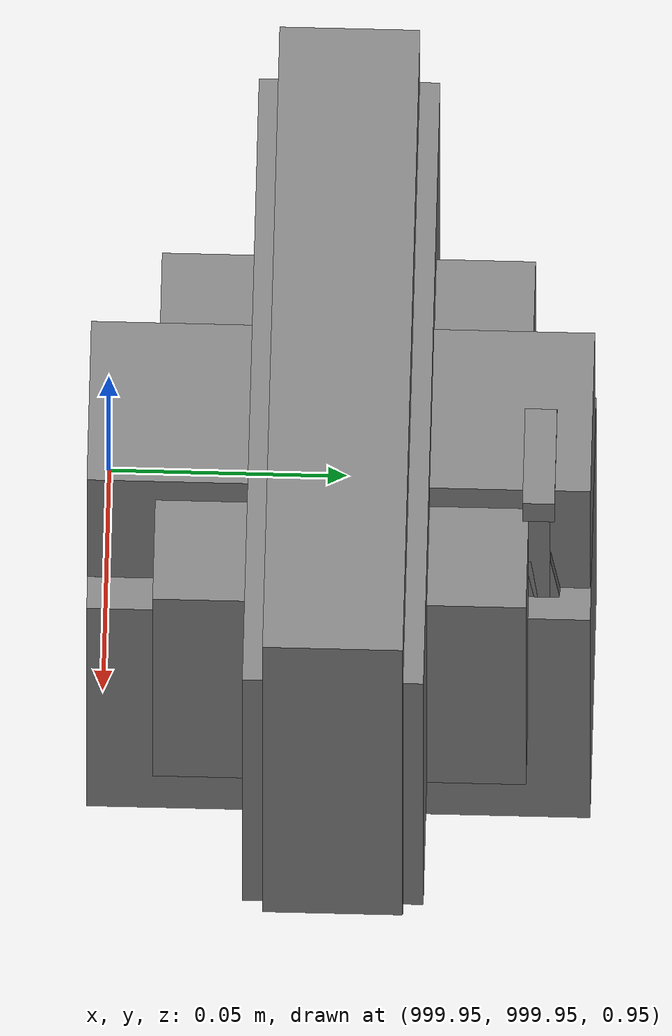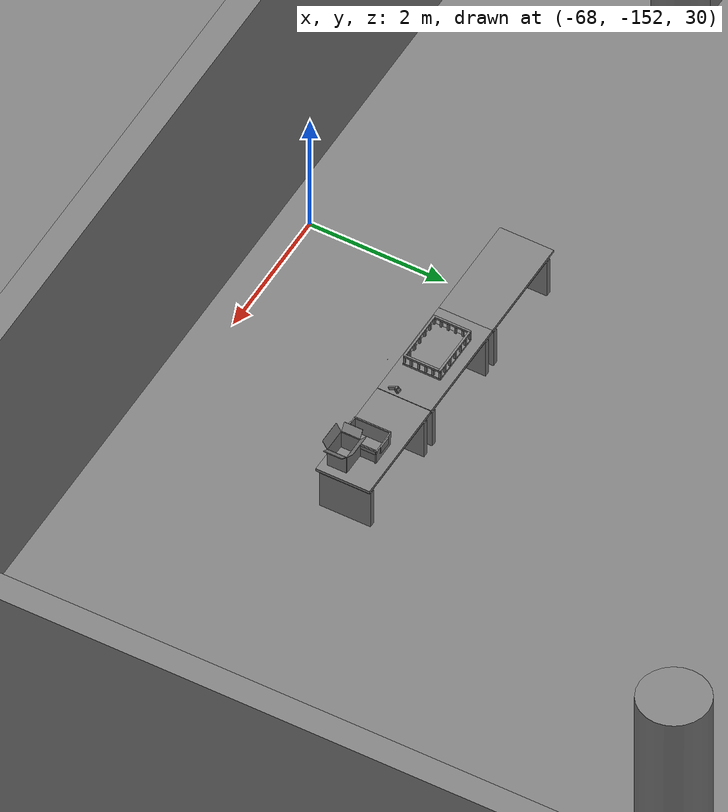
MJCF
<mujoco>
    <option gravity="0.000000000 0.000000000 -9.810000420" timestep="0.0049999999" integrator="implicitfast" density="1.225" viscosity="1.8000001e-05" noslip_iterations="10" iterations="100" sdf_iterations="50">
        <flag multiccd="disable"/>
    </option>
    <size memory="1000M"/>
    <compiler coordinate="local"/>
    <worldbody>
        <light cutoff="30" pos="0 1 1" dir="0 -1 -2"/>
        <light cutoff="30" pos="0 -1 1" dir="0 1 -2"/>
        <body pos="-64.866622925 -149.383972168 30.183746338" euler="89.999984741 89.999946594 0.000000000" name="openloong_gripper_2f85_fix_base_usda_bluebox_01">
            <geom contype="1" conaffinity="1" density="1000" type="box" material="" rgba="0.500000000 0.500000000 0.500000000 1.000000000" solimp="0.899999976 0.949999988 0.001000000" friction="1.000000000 0.005000000 0.000100000" solref="0.020000000 1.000000000" margin="0" condim="3" group="0" pos="0.276580811 0.187225342 0.000068665" quat="0.707106948 0.000077471 0.707106352 0.000077486" size="0.100000001 0.057999998 0.010000000" name="openloong_gripper_2f85_fix_base_usda_geom_B15E7EC6_732D_4BF1_904F_D3518C912A2D"/>
            <geom contype="1" conaffinity="1" density="1000" type="box" material="" rgba="0.500000000 0.500000000 0.500000000 1.000000000" solimp="0.899999976 0.949999988 0.001000000" friction="1.000000000 0.005000000 0.000100000" solref="0.020000000 1.000000000" margin="0" condim="3" group="0" pos="0.000000000 0.002883911 0.000000000" quat="0.999999881 0.000000000 0.000000000 0.000000000" size="0.254000008 0.003000000 0.172000006" name="openloong_gripper_2f85_fix_base_usda_geom_36135B7F_A87F_4267_B1D2_6B99813098CB"/>
            <geom contype="1" conaffinity="1" density="1000" type="box" material="" rgba="0.500000000 0.500000000 0.500000000 1.000000000" solimp="0.899999976 0.949999988 0.001000000" friction="1.000000000 0.005000000 0.000100000" solref="0.020000000 1.000000000" margin="0" condim="3" group="0" pos="0.000000000 0.124874115 0.173484802" quat="0.999796331 0.020176515 -0.000000015 0.000000030" size="0.259999990 0.119999997 0.007000000" name="openloong_gripper_2f85_fix_base_usda_geom_7741B61B_068A_48F9_9EB7_BDE553051311"/>
            <geom contype="1" conaffinity="1" density="1000" type="box" material="" rgba="0.500000000 0.500000000 0.500000000 1.000000000" solimp="0.899999976 0.949999988 0.001000000" friction="1.000000000 0.005000000 0.000100000" solref="0.020000000 1.000000000" margin="0" condim="3" group="0" pos="0.000000000 0.124874115 -0.173469543" quat="0.999796331 -0.020176545 -0.000000015 0.000000000" size="0.259999990 0.119999997 0.007000000" name="openloong_gripper_2f85_fix_base_usda_geom_1AC87A98_C35B_4DB8_B217_F6C1B620EF2F"/>
            <geom contype="1" conaffinity="1" density="1000" type="box" material="" rgba="0.500000000 0.500000000 0.500000000 1.000000000" solimp="0.899999976 0.949999988 0.001000000" friction="1.000000000 0.005000000 0.000100000" solref="0.020000000 1.000000000" margin="0" condim="3" group="0" pos="0.000000000 0.214008331 0.188980103" quat="0.999912977 0.013176724 0.000000015 0.000000000" size="0.259999990 0.029999999 0.012500000" name="openloong_gripper_2f85_fix_base_usda_geom_2CFB10D3_7C3E_42C3_9349_669AD07FC376"/>
            <geom contype="1" conaffinity="1" density="1000" type="box" material="" rgba="0.500000000 0.500000000 0.500000000 1.000000000" solimp="0.899999976 0.949999988 0.001000000" friction="1.000000000 0.005000000 0.000100000" solref="0.020000000 1.000000000" margin="0" condim="3" group="0" pos="-0.258361816 0.125289917 0.001876831" quat="0.702796936 -0.020792112 0.710783124 0.020769298" size="0.189999998 0.119999997 0.009000000" name="openloong_gripper_2f85_fix_base_usda_geom_031E9821_E13B_4282_B105_DAF227CC4C42"/>
            <geom contype="1" conaffinity="1" density="1000" type="box" material="" rgba="0.500000000 0.500000000 0.500000000 1.000000000" solimp="0.899999976 0.949999988 0.001000000" friction="1.000000000 0.005000000 0.000100000" solref="0.020000000 1.000000000" margin="0" condim="3" group="0" pos="0.000000000 0.214008331 -0.188980103" quat="0.999912977 -0.013176769 0.000000030 0.000000015" size="0.259999990 0.029999999 0.012500000" name="openloong_gripper_2f85_fix_base_usda_geom_EBA479EC_343C_417E_9D10_E58158C00B62"/>
            <geom contype="1" conaffinity="1" density="1000" type="box" material="" rgba="0.500000000 0.500000000 0.500000000 1.000000000" solimp="0.899999976 0.949999988 0.001000000" friction="1.000000000 0.005000000 0.000100000" solref="0.020000000 1.000000000" margin="0" condim="3" group="0" pos="-0.276611328 0.187225342 0.000068665" quat="0.707106650 0.000077441 0.707106709 0.000077456" size="0.100000001 0.057999998 0.010000000" name="openloong_gripper_2f85_fix_base_usda_geom_164FBEC4_36AF_40C9_BA6F_7430B04055B2"/>
            <geom contype="1" conaffinity="1" density="1000" type="box" material="" rgba="0.500000000 0.500000000 0.500000000 1.000000000" solimp="0.899999976 0.949999988 0.001000000" friction="1.000000000 0.005000000 0.000100000" solref="0.020000000 1.000000000" margin="0" condim="3" group="0" pos="0.258331299 0.125289917 0.001876831" quat="0.702851415 0.018856421 0.710823774 -0.019329369" size="0.189999998 0.119999997 0.009000000" name="openloong_gripper_2f85_fix_base_usda_geom_D466DAD3_575F_4A2A_BBE9_56A3A5E7DBE4"/>
            <freejoint name="openloong_gripper_2f85_fix_base_usda_bluebox_01_joint"/>
            <site size="0.005000000 0.005000000 0.005000000" rgba="0.500000000 0.500000000 0.500000000 1.000000000" pos="0.000000000 0.000000000 0.000000000" quat="0.999961913 0.008726534 0.000000000 0.000000000" group="0" type="sphere" name="openloong_gripper_2f85_fix_base_usda_bluebox_01site"/>
        </body>
        <body pos="-64.496299744 -149.491867065 30.235729218" euler="0.000000000 0.000000000 89.999946594" name="openloong_gripper_2f85_fix_base_usda_cardboardbox_01">
            <geom contype="1" conaffinity="1" density="1000" type="box" material="" rgba="0.500000000 0.500000000 0.500000000 1.000000000" solimp="0.899999976 0.949999988 0.001000000" friction="1.000000000 0.005000000 0.000100000" solref="0.020000000 1.000000000" margin="0" condim="3" group="0" pos="-0.003166199 -0.004086494 0.005052090" quat="1.000000000 0.000000000 0.000000000 0.000000000" size="0.142499998 0.177500010 0.005000000" name="openloong_gripper_2f85_fix_base_usda_geom_96DD76FB_5A5D_4716_9249_C276C1A5B7C8"/>
            <geom contype="1" conaffinity="1" density="1000" type="box" material="" rgba="0.500000000 0.500000000 0.500000000 1.000000000" solimp="0.899999976 0.949999988 0.001000000" friction="1.000000000 0.005000000 0.000100000" solref="0.020000000 1.000000000" margin="0" condim="3" group="0" pos="-0.003166199 0.170316696 0.150570869" quat="1.000000000 0.000000000 0.000000000 0.000000000" size="0.142499998 0.005000000 0.149999991" name="openloong_gripper_2f85_fix_base_usda_geom_DF84F5AD_CC92_41F7_A119_D0529809EE74"/>
            <geom contype="1" conaffinity="1" density="1000" type="box" material="" rgba="0.500000000 0.500000000 0.500000000 1.000000000" solimp="0.899999976 0.949999988 0.001000000" friction="1.000000000 0.005000000 0.000100000" solref="0.020000000 1.000000000" margin="0" condim="3" group="0" pos="-0.147399902 -0.005307198 0.150570869" quat="1.000000000 0.000000000 0.000000000 0.000000000" size="0.005000000 0.177500010 0.149999991" name="openloong_gripper_2f85_fix_base_usda_geom_5DC94CA1_E5D5_49FD_BAC2_E00E6E94A8C6"/>
            <geom contype="1" conaffinity="1" density="1000" type="box" material="" rgba="0.500000000 0.500000000 0.500000000 1.000000000" solimp="0.899999976 0.949999988 0.001000000" friction="1.000000000 0.005000000 0.000100000" solref="0.020000000 1.000000000" margin="0" condim="3" group="0" pos="0.140275955 -0.005307198 0.150570869" quat="1.000000000 0.000000000 0.000000000 0.000000000" size="0.005000000 0.177500010 0.149999991" name="openloong_gripper_2f85_fix_base_usda_geom_9E1ABCEE_3952_4510_B4A5_0EF1AF1F80B8"/>
            <geom contype="1" conaffinity="1" density="1000" type="box" material="" rgba="0.500000000 0.500000000 0.500000000 1.000000000" solimp="0.899999976 0.949999988 0.001000000" friction="1.000000000 0.005000000 0.000100000" solref="0.020000000 1.000000000" margin="0" condim="3" group="0" pos="-0.003166199 -0.181550980 0.150570869" quat="1.000000000 0.000000000 0.000000000 0.000000000" size="0.142499998 0.005000000 0.149999991" name="openloong_gripper_2f85_fix_base_usda_geom_C4630B86_9D4F_458C_BF55_92B02EA405AB"/>
            <freejoint name="openloong_gripper_2f85_fix_base_usda_cardboardbox_01_joint"/>
            <site size="0.005000000 0.005000000 0.005000000" rgba="0.500000000 0.500000000 0.500000000 1.000000000" pos="0.000000000 0.000000000 0.000000000" quat="0.999961913 0.008726535 0.000000000 0.000000000" group="0" type="sphere" name="openloong_gripper_2f85_fix_base_usda_site_5425A571_2F47_455F_9024_2C317372CD0B"/>
            <body pos="0.139160156 -0.004048347 0.301930904" euler="-179.999954224 49.383502960 179.999954224" name="openloong_gripper_2f85_fix_base_usda_A1_006">
                <geom contype="1" conaffinity="1" density="1000" type="box" material="" rgba="0.500000000 0.500000000 0.500000000 1.000000000" solimp="0.899999976 0.949999988 0.001000000" friction="1.000000000 0.005000000 0.000100000" solref="0.020000000 1.000000000" margin="0" condim="3" group="0" pos="-0.071587563 0.000009537 0.001745224" quat="0.999999881 0.000000000 0.000000000 0.000000000" size="0.071249999 0.179999992 0.002500000" name="openloong_gripper_2f85_fix_base_usda_geom_0E58368D_7C69_493E_8A9F_B745661A88C4"/>
                <joint armature="0" stiffness="0.07" damping="0.0099999998" axis="0.000000 1.000000 0.000000" type="hinge" name="openloong_gripper_2f85_fix_base_usda_A1_006"/>
            </body>
            <body pos="-0.145902634 -0.004086494 0.301938057" euler="-180.000000000 -60.000011444 -180.000000000" name="openloong_gripper_2f85_fix_base_usda_A2_006">
                <geom contype="1" conaffinity="1" density="1000" type="box" material="" rgba="0.500000000 0.500000000 0.500000000 1.000000000" solimp="0.899999976 0.949999988 0.001000000" friction="1.000000000 0.005000000 0.000100000" solref="0.020000000 1.000000000" margin="0" condim="3" group="0" pos="0.071268082 0.000009537 0.002717972" quat="0.000002921 0.000000000 -0.000000030 0.999999881" size="0.071249999 0.179999992 0.002500000" name="openloong_gripper_2f85_fix_base_usda_geom_EDD2A472_972C_4A45_A224_9FAD788F34DA"/>
                <joint armature="0" stiffness="0.07" damping="0.0099999998" axis="0.000000 1.000000 0.000000" type="hinge" name="openloong_gripper_2f85_fix_base_usda_A2_006"/>
            </body>
            <body pos="-0.003385544 0.175991058 0.301930904" euler="-125.858116150 -0.000004561 0.000002331" name="openloong_gripper_2f85_fix_base_usda_B2_006">
                <geom contype="1" conaffinity="1" density="1000" type="box" material="" rgba="0.500000000 0.500000000 0.500000000 1.000000000" solimp="0.899999976 0.949999988 0.001000000" friction="1.000000000 0.005000000 0.000100000" solref="0.020000000 1.000000000" margin="0" condim="3" group="0" pos="0.000009537 -0.070939064 -0.002470016" quat="0.999614120 0.027776197 -0.000000015 0.000000030" size="0.137500003 0.064999998 0.005000000" name="openloong_gripper_2f85_fix_base_usda_geom_3821B85F_734C_443C_811F_E4B26F1C68B8"/>
                <joint armature="0" stiffness="0.07" damping="0.0099999998" axis="1.000000 0.000000 0.000000" type="hinge" name="openloong_gripper_2f85_fix_base_usda_B2_006"/>
            </body>
            <body pos="-0.003385544 -0.184140205 0.301938057" euler="147.805557251 0.000000000 0.000000000" name="openloong_gripper_2f85_fix_base_usda_B1_006">
                <geom contype="1" conaffinity="1" density="1000" type="box" material="" rgba="0.500000000 0.500000000 0.500000000 1.000000000" solimp="0.899999976 0.949999988 0.001000000" friction="1.000000000 0.005000000 0.000100000" solref="0.020000000 1.000000000" margin="0" condim="3" group="0" pos="-0.000028610 0.070202351 -0.002703667" quat="0.999614179 -0.027776167 0.000000000 0.000000000" size="0.137500003 0.064999998 0.005000000" name="openloong_gripper_2f85_fix_base_usda_geom_6030C7D0_8D60_4631_B7FF_65F1173AB88D"/>
                <joint armature="0" stiffness="0.07" damping="0.0099999998" axis="1.000000 0.000000 0.000000" type="hinge" name="openloong_gripper_2f85_fix_base_usda_B1_006"/>
            </body>
        </body>
        <body pos="-65.882858276 -149.481979370 30.229999542" euler="-64.487716675 0.000000000 0.000000000" name="openloong_gripper_2f85_fix_base_usda_Barcode">
            <geom contype="1" conaffinity="1" density="1000" type="box" material="" rgba="0.500000000 0.500000000 0.500000000 1.000000000" solimp="0.899999976 0.949999988 0.001000000" friction="1.000000000 0.005000000 0.000100000" solref="0.020000000 1.000000000" margin="0" condim="3" group="0" pos="0.000000000 0.013038635 0.001419067" quat="0.000000000 0.000000000 0.000000000 1.000000119" size="0.034000002 0.010000000 0.017999999" name="openloong_gripper_2f85_fix_base_usda_geom_D45FA82B_3D8D_462D_99CD_0ED7C5FB1FAE"/>
            <geom contype="1" conaffinity="1" density="1000" type="box" material="" rgba="0.500000000 0.500000000 0.500000000 1.000000000" solimp="0.899999976 0.949999988 0.001000000" friction="1.000000000 0.005000000 0.000100000" solref="0.020000000 1.000000000" margin="0" condim="3" group="0" pos="0.000000000 -0.035301208 -0.007095337" quat="0.000000000 0.000000000 -0.043619365 0.999048233" size="0.028999999 0.010000000 0.020000000" name="openloong_gripper_2f85_fix_base_usda_geom_8DF0DF1F_B955_4A66_97F7_891FB0B706E7"/>
            <geom contype="1" conaffinity="1" density="1000" type="box" material="" rgba="0.500000000 0.500000000 0.500000000 1.000000000" solimp="0.899999976 0.949999988 0.001000000" friction="1.000000000 0.005000000 0.000100000" solref="0.020000000 1.000000000" margin="0" condim="3" group="0" pos="0.000000000 -0.043411255 -0.011749268" quat="0.922262907 0.386563420 0.000000000 0.000000000" size="0.026000001 0.010000000 0.020000000" name="openloong_gripper_2f85_fix_base_usda_geom_A3D41E7E_1A8D_467C_A0D4_119E98C971DE"/>
            <geom contype="1" conaffinity="1" density="1000" type="box" material="" rgba="0.500000000 0.500000000 0.500000000 1.000000000" solimp="0.899999976 0.949999988 0.001000000" friction="1.000000000 0.005000000 0.000100000" solref="0.020000000 1.000000000" margin="0" condim="3" group="0" pos="0.000000000 -0.016967773 -0.031860352" quat="0.000000000 0.000000000 0.000000000 1.000000119" size="0.008000000 0.010000000 0.013000000" name="openloong_gripper_2f85_fix_base_usda_geom_8A618CD3_9DC2_41AF_B5EB_98F3195BDA56"/>
            <geom contype="1" conaffinity="1" density="1000" type="box" material="" rgba="0.500000000 0.500000000 0.500000000 1.000000000" solimp="0.899999976 0.949999988 0.001000000" friction="1.000000000 0.005000000 0.000100000" solref="0.020000000 1.000000000" margin="0" condim="3" group="0" pos="0.000000000 -0.001869202 0.000312805" quat="0.953716993 0.300705761 0.000000000 0.000000000" size="0.032000002 0.010000000 0.018999999" name="openloong_gripper_2f85_fix_base_usda_geom_1BEB7235_17C6_474F_9AD5_E49FD0F362C4"/>
            <geom contype="1" conaffinity="1" density="1000" type="box" material="" rgba="0.500000000 0.500000000 0.500000000 1.000000000" solimp="0.899999976 0.949999988 0.001000000" friction="1.000000000 0.005000000 0.000100000" solref="0.020000000 1.000000000" margin="0" condim="3" group="0" pos="0.000000000 -0.019531250 -0.003173828" quat="0.953716993 0.300705761 0.000000000 0.000000000" size="0.030999999 0.010000000 0.020000000" name="openloong_gripper_2f85_fix_base_usda_geom_AACE581C_3DA8_4AFA_A247_AD99C32F001F"/>
            <geom contype="1" conaffinity="1" density="1000" type="box" material="" rgba="0.500000000 0.500000000 0.500000000 1.000000000" solimp="0.899999976 0.949999988 0.001000000" friction="1.000000000 0.005000000 0.000100000" solref="0.020000000 1.000000000" margin="0" condim="3" group="0" pos="0.000000000 -0.035301208 -0.007095337" quat="0.953716993 0.300705761 0.000000000 0.000000000" size="0.028999999 0.010000000 0.020000000" name="openloong_gripper_2f85_fix_base_usda_geom_42CE84C6_E023_47AC_A7CD_CC2606B6BBAE"/>
            <geom contype="1" conaffinity="1" density="1000" type="box" material="" rgba="0.500000000 0.500000000 0.500000000 1.000000000" solimp="0.899999976 0.949999988 0.001000000" friction="1.000000000 0.005000000 0.000100000" solref="0.020000000 1.000000000" margin="0" condim="3" group="0" pos="0.000000000 -0.042617798 -0.071121216" quat="0.000000000 0.000000000 0.000000000 1.000000119" size="0.013000000 0.021000000 0.059999999" name="openloong_gripper_2f85_fix_base_usda_geom_D9DDF04D_A42F_467E_9174_4AA676E8A7C0"/>
            <freejoint name="openloong_gripper_2f85_fix_base_usda_Barcode_joint"/>
            <site size="0.005000000 0.005000000 0.005000000" rgba="0.500000000 0.500000000 0.500000000 1.000000000" pos="0.000000000 0.000000000 0.000000000" quat="1.000000000 0.000000000 0.000000000 0.000000000" group="0" type="sphere" name="openloong_gripper_2f85_fix_base_usda_Barcode_site"/>
        </body>
        <body pos="-66.745018005 -149.392349243 30.184000015" euler="0.000000000 0.000000000 89.999946594" name="[22331328551867]_Basket_01">
            <geom contype="1" conaffinity="1" density="1000" type="box" material="" rgba="0.500000000 0.500000000 0.500000000 1.000000000" solimp="0.899999976 0.949999988 0.001000000" friction="1.000000000 0.005000000 0.000100000" solref="0.020000000 1.000000000" margin="0" condim="3" group="0" pos="-0.052425385 0.389207840 0.089787483" quat="0.707107008 0.000000000 0.000000000 0.707106411" size="0.014249999 0.014249999 0.059999999" name="[22331328551867]_geom_97F35192_C50D_471C_9F01_3C5526B6DAD4"/>
            <geom contype="1" conaffinity="1" density="1000" type="box" material="" rgba="0.500000000 0.500000000 0.500000000 1.000000000" solimp="0.899999976 0.949999988 0.001000000" friction="1.000000000 0.005000000 0.000100000" solref="0.020000000 1.000000000" margin="0" condim="3" group="0" pos="0.264015198 -0.133043289 0.089787483" quat="0.707107008 0.000000000 0.000000000 0.707106411" size="0.014249999 0.014249999 0.059999999" name="[22331328551867]_geom_40857BF1_B9CD_47A8_B3D5_7F41C6E987E7"/>
            <geom contype="1" conaffinity="1" density="1000" type="box" material="" rgba="0.500000000 0.500000000 0.500000000 1.000000000" solimp="0.899999976 0.949999988 0.001000000" friction="1.000000000 0.005000000 0.000100000" solref="0.020000000 1.000000000" margin="0" condim="3" group="0" pos="-0.264015198 -0.265548706 0.089793205" quat="0.707107008 0.000000000 0.000000000 0.707106411" size="0.014249999 0.014249999 0.059999999" name="[22331328551867]_geom_147BA8AC_8866_4F4C_8929_01FE17646504"/>
            <geom contype="1" conaffinity="1" density="1000" type="box" material="" rgba="0.500000000 0.500000000 0.500000000 1.000000000" solimp="0.899999976 0.949999988 0.001000000" friction="1.000000000 0.005000000 0.000100000" solref="0.020000000 1.000000000" margin="0" condim="3" group="0" pos="-0.160263062 -0.389322281 0.089793205" quat="0.707107008 0.000000000 0.000000000 0.707106411" size="0.014249999 0.014249999 0.059999999" name="[22331328551867]_geom_EE3732C2_9380_493F_88B2_B60AB8FBEDA2"/>
            <geom contype="1" conaffinity="1" density="1000" type="box" material="" rgba="0.500000000 0.500000000 0.500000000 1.000000000" solimp="0.899999976 0.949999988 0.001000000" friction="1.000000000 0.005000000 0.000100000" solref="0.020000000 1.000000000" margin="0" condim="3" group="0" pos="0.162265778 -0.389322281 0.089787483" quat="0.707107008 0.000000000 0.000000000 0.707106411" size="0.014249999 0.014249999 0.059999999" name="[22331328551867]_geom_36CB8CB2_F26E_415B_983B_59DF19BED40C"/>
            <geom contype="1" conaffinity="1" density="1000" type="box" material="" rgba="0.500000000 0.500000000 0.500000000 1.000000000" solimp="0.899999976 0.949999988 0.001000000" friction="1.000000000 0.005000000 0.000100000" solref="0.020000000 1.000000000" margin="0" condim="3" group="0" pos="0.264015198 0.389207840 0.089787483" quat="0.707107008 0.000000000 0.000000000 0.707106411" size="0.014249999 0.014249999 0.059999999" name="[22331328551867]_geom_219C28C8_99C8_4AC9_855F_E95C76008D17"/>
            <geom contype="1" conaffinity="1" density="1000" type="box" material="" rgba="0.500000000 0.500000000 0.500000000 1.000000000" solimp="0.899999976 0.949999988 0.001000000" friction="1.000000000 0.005000000 0.000100000" solref="0.020000000 1.000000000" margin="0" condim="3" group="0" pos="-0.264015198 -0.133043289 0.089793205" quat="0.707107008 0.000000000 0.000000000 0.707106411" size="0.014249999 0.014249999 0.059999999" name="[22331328551867]_geom_586265F8_CE7D_4C95_A4E5_1B7120329324"/>
            <geom contype="1" conaffinity="1" density="1000" type="box" material="" rgba="0.500000000 0.500000000 0.500000000 1.000000000" solimp="0.899999976 0.949999988 0.001000000" friction="1.000000000 0.005000000 0.000100000" solref="0.020000000 1.000000000" margin="0" condim="3" group="0" pos="-0.264026642 0.269256592 0.089793205" quat="0.707107008 0.000000000 0.000000000 0.707106411" size="0.014249999 0.014249999 0.059999999" name="[22331328551867]_geom_F71E9098_B9AB_4817_8AB7_5C71D4F74491"/>
            <geom contype="1" conaffinity="1" density="1000" type="box" material="" rgba="0.500000000 0.500000000 0.500000000 1.000000000" solimp="0.899999976 0.949999988 0.001000000" friction="1.000000000 0.005000000 0.000100000" solref="0.020000000 1.000000000" margin="0" condim="3" group="0" pos="0.054462433 0.389207840 0.089787483" quat="0.707107008 0.000000000 0.000000000 0.707106411" size="0.014249999 0.014249999 0.059999999" name="[22331328551867]_geom_67C6D7D4_29F4_466D_9E89_03C40A41CB8C"/>
            <geom contype="1" conaffinity="1" density="1000" type="box" material="" rgba="0.500000000 0.500000000 0.500000000 1.000000000" solimp="0.899999976 0.949999988 0.001000000" friction="1.000000000 0.005000000 0.000100000" solref="0.020000000 1.000000000" margin="0" condim="3" group="0" pos="0.054462433 -0.389322281 0.089787483" quat="0.707107008 0.000000000 0.000000000 0.707106411" size="0.014249999 0.014249999 0.059999999" name="[22331328551867]_geom_EC5852FB_AE87_494B_8BA6_B66B72ABEAAD"/>
            <geom contype="1" conaffinity="1" density="1000" type="box" material="" rgba="0.500000000 0.500000000 0.500000000 1.000000000" solimp="0.899999976 0.949999988 0.001000000" friction="1.000000000 0.005000000 0.000100000" solref="0.020000000 1.000000000" margin="0" condim="3" group="0" pos="0.264015198 0.269256592 0.089793205" quat="0.707107008 0.000000000 0.000000000 0.707106411" size="0.014249999 0.014249999 0.059999999" name="[22331328551867]_geom_F1C40C31_710B_4E6D_B957_295FBE92397A"/>
            <geom contype="1" conaffinity="1" density="1000" type="box" material="" rgba="0.500000000 0.500000000 0.500000000 1.000000000" solimp="0.899999976 0.949999988 0.001000000" friction="1.000000000 0.005000000 0.000100000" solref="0.020000000 1.000000000" margin="0" condim="3" group="0" pos="0.264015198 -0.389322281 0.089787483" quat="0.707107008 0.000000000 0.000000000 0.707106411" size="0.014249999 0.014249999 0.059999999" name="[22331328551867]_geom_31F9476B_B3F5_42AB_87AB_1A5181CE386C"/>
            <geom contype="1" conaffinity="1" density="1000" type="box" material="" rgba="0.500000000 0.500000000 0.500000000 1.000000000" solimp="0.899999976 0.949999988 0.001000000" friction="1.000000000 0.005000000 0.000100000" solref="0.020000000 1.000000000" margin="0" condim="3" group="0" pos="0.000000000 0.000000000 0.015998840" quat="0.707107008 0.000000000 0.000000000 0.707106411" size="0.403499991 0.279000014 0.015750000" name="[22331328551867]_geom_18BB4291_927E_4D78_9983_BABC05C0DFD6"/>
            <geom contype="1" conaffinity="1" density="1000" type="box" material="" rgba="0.500000000 0.500000000 0.500000000 1.000000000" solimp="0.899999976 0.949999988 0.001000000" friction="1.000000000 0.005000000 0.000100000" solref="0.020000000 1.000000000" margin="0" condim="3" group="0" pos="0.000000000 -0.389476776 0.163619041" quat="0.707107008 0.000000000 0.000000000 0.707106411" size="0.015000000 0.277500004 0.015750000" name="[22331328551867]_geom_B2A1B9B6_EBAB_436C_862A_8F626E79DCB4"/>
            <geom contype="1" conaffinity="1" density="1000" type="box" material="" rgba="0.500000000 0.500000000 0.500000000 1.000000000" solimp="0.899999976 0.949999988 0.001000000" friction="1.000000000 0.005000000 0.000100000" solref="0.020000000 1.000000000" margin="0" condim="3" group="0" pos="0.162265778 0.389207840 0.089787483" quat="0.707107008 0.000000000 0.000000000 0.707106411" size="0.014249999 0.014249999 0.059999999" name="[22331328551867]_geom_75E48F68_758D_4604_B6DE_AF8287C619C2"/>
            <geom contype="1" conaffinity="1" density="1000" type="box" material="" rgba="0.500000000 0.500000000 0.500000000 1.000000000" solimp="0.899999976 0.949999988 0.001000000" friction="1.000000000 0.005000000 0.000100000" solref="0.020000000 1.000000000" margin="0" condim="3" group="0" pos="0.000000000 0.389471054 0.163619041" quat="0.707107008 0.000000000 0.000000000 0.707106411" size="0.015000000 0.277500004 0.015750000" name="[22331328551867]_geom_A7D6EAB1_2739_4D5C_ACC8_3F5CFF42F708"/>
            <geom contype="1" conaffinity="1" density="1000" type="box" material="" rgba="0.500000000 0.500000000 0.500000000 1.000000000" solimp="0.899999976 0.949999988 0.001000000" friction="1.000000000 0.005000000 0.000100000" solref="0.020000000 1.000000000" margin="0" condim="3" group="0" pos="-0.263511658 0.000000000 0.163619041" quat="0.707107008 0.000000000 0.000000000 0.707106411" size="0.403499991 0.015000000 0.015750000" name="[22331328551867]_geom_EEF3ECC9_37D8_4342_8E8F_0F1D481A93BC"/>
            <geom contype="1" conaffinity="1" density="1000" type="box" material="" rgba="0.500000000 0.500000000 0.500000000 1.000000000" solimp="0.899999976 0.949999988 0.001000000" friction="1.000000000 0.005000000 0.000100000" solref="0.020000000 1.000000000" margin="0" condim="3" group="0" pos="-0.264015198 0.141334534 0.089793205" quat="0.707107008 0.000000000 0.000000000 0.707106411" size="0.014249999 0.014249999 0.059999999" name="[22331328551867]_geom_52D1FF45_404D_4953_9E06_142D24F3FDEC"/>
            <geom contype="1" conaffinity="1" density="1000" type="box" material="" rgba="0.500000000 0.500000000 0.500000000 1.000000000" solimp="0.899999976 0.949999988 0.001000000" friction="1.000000000 0.005000000 0.000100000" solref="0.020000000 1.000000000" margin="0" condim="3" group="0" pos="0.264015198 -0.265548706 0.089787483" quat="0.707107008 0.000000000 0.000000000 0.707106411" size="0.014249999 0.014249999 0.059999999" name="[22331328551867]_geom_AD013D1F_591F_4A38_835A_50699E02D415"/>
            <geom contype="1" conaffinity="1" density="1000" type="box" material="" rgba="0.500000000 0.500000000 0.500000000 1.000000000" solimp="0.899999976 0.949999988 0.001000000" friction="1.000000000 0.005000000 0.000100000" solref="0.020000000 1.000000000" margin="0" condim="3" group="0" pos="-0.160263062 0.389207840 0.089787483" quat="0.707107008 0.000000000 0.000000000 0.707106411" size="0.014249999 0.014249999 0.059999999" name="[22331328551867]_geom_C51D8809_6FFC_4038_A15B_F98FE5C29401"/>
            <geom contype="1" conaffinity="1" density="1000" type="box" material="" rgba="0.500000000 0.500000000 0.500000000 1.000000000" solimp="0.899999976 0.949999988 0.001000000" friction="1.000000000 0.005000000 0.000100000" solref="0.020000000 1.000000000" margin="0" condim="3" group="0" pos="-0.052425385 -0.389322281 0.089787483" quat="0.707107008 0.000000000 0.000000000 0.707106411" size="0.014249999 0.014249999 0.059999999" name="[22331328551867]_geom_9F237EFB_13CE_4822_9157_DBA39C599932"/>
            <geom contype="1" conaffinity="1" density="1000" type="box" material="" rgba="0.500000000 0.500000000 0.500000000 1.000000000" solimp="0.899999976 0.949999988 0.001000000" friction="1.000000000 0.005000000 0.000100000" solref="0.020000000 1.000000000" margin="0" condim="3" group="0" pos="-0.264026642 -0.389322281 0.089793205" quat="0.707107008 0.000000000 0.000000000 0.707106411" size="0.014249999 0.014249999 0.059999999" name="[22331328551867]_geom_9B79E956_88D4_4D1B_9CEC_C826878B668E"/>
            <geom contype="1" conaffinity="1" density="1000" type="box" material="" rgba="0.500000000 0.500000000 0.500000000 1.000000000" solimp="0.899999976 0.949999988 0.001000000" friction="1.000000000 0.005000000 0.000100000" solref="0.020000000 1.000000000" margin="0" condim="3" group="0" pos="0.264015198 0.141334534 0.089787483" quat="0.707107008 0.000000000 0.000000000 0.707106411" size="0.014249999 0.014249999 0.059999999" name="[22331328551867]_geom_E645F897_3374_4F89_9887_7919D5F7BB85"/>
            <geom contype="1" conaffinity="1" density="1000" type="box" material="" rgba="0.500000000 0.500000000 0.500000000 1.000000000" solimp="0.899999976 0.949999988 0.001000000" friction="1.000000000 0.005000000 0.000100000" solref="0.020000000 1.000000000" margin="0" condim="3" group="0" pos="-0.264015198 0.389207840 0.089793205" quat="0.707107008 0.000000000 0.000000000 0.707106411" size="0.014249999 0.014249999 0.059999999" name="[22331328551867]_geom_2AB9D33B_7466_4ACD_97F6_4AE3C6789022"/>
            <geom contype="1" conaffinity="1" density="1000" type="box" material="" rgba="0.500000000 0.500000000 0.500000000 1.000000000" solimp="0.899999976 0.949999988 0.001000000" friction="1.000000000 0.005000000 0.000100000" solref="0.020000000 1.000000000" margin="0" condim="3" group="0" pos="0.264015198 0.004480362 0.089787483" quat="0.707107008 0.000000000 0.000000000 0.707106411" size="0.014249999 0.014249999 0.059999999" name="[22331328551867]_geom_39E173F5_A0F6_46CB_9690_9FCD45F1EFE5"/>
            <geom contype="1" conaffinity="1" density="1000" type="box" material="" rgba="0.500000000 0.500000000 0.500000000 1.000000000" solimp="0.899999976 0.949999988 0.001000000" friction="1.000000000 0.005000000 0.000100000" solref="0.020000000 1.000000000" margin="0" condim="3" group="0" pos="0.263694763 -0.000011444 0.163619041" quat="0.707107008 0.000000000 0.000000000 0.707106411" size="0.403499991 0.015000000 0.015750000" name="[22331328551867]_geom_82979A32_883E_42E7_915C_886B2A966ACB"/>
            <geom contype="1" conaffinity="1" density="1000" type="box" material="" rgba="0.500000000 0.500000000 0.500000000 1.000000000" solimp="0.899999976 0.949999988 0.001000000" friction="1.000000000 0.005000000 0.000100000" solref="0.020000000 1.000000000" margin="0" condim="3" group="0" pos="-0.264015198 0.004480362 0.089793205" quat="0.707107008 0.000000000 0.000000000 0.707106411" size="0.014249999 0.014249999 0.059999999" name="[22331328551867]_geom_994C1514_40D8_43CE_9BD4_D8C2E8FE1501"/>
            <freejoint name="[22331328551867]_joint_0B5533A4_A941_42C6_8F6E_1231B9497BF5"/>
        </body>
        <body pos="0.000000000 0.000000000 0.000000000" euler="0.000000000 0.000000000 0.000000000" name="Static Objects_Static Objects">
            <geom contype="1" conaffinity="1" density="1000" type="box" material="" rgba="0.500000000 0.500000000 0.500000000 1.000000000" solimp="0.899999976 0.949999988 0.001000000" friction="1.000000000 0.005000000 0.000100000" solref="0.020000000 1.000000000" margin="0" condim="3" group="0" pos="-67.544113159 -149.365814209 29.727830887" quat="0.500000417 0.499999970 0.499999553 0.499999970" size="0.381000012 0.319999993 0.041000001" name="Static Objects_geom_0EA7CB2F_B88F_49F2_AC41_EAF03EFCC234"/>
            <geom contype="1" conaffinity="1" density="1000" type="box" material="" rgba="0.500000000 0.500000000 0.500000000 1.000000000" solimp="0.899999976 0.949999988 0.001000000" friction="1.000000000 0.005000000 0.000100000" solref="0.020000000 1.000000000" margin="0" condim="3" group="0" pos="-68.239501953 -149.365814209 30.086868286" quat="0.500000417 0.499999970 0.499999553 0.499999970" size="0.370999992 0.039500002 0.745000005" name="Static Objects_geom_6533A113_600A_4F39_82F9_9CBC46E9285A"/>
            <geom contype="1" conaffinity="1" density="1000" type="box" material="" rgba="0.500000000 0.500000000 0.500000000 1.000000000" solimp="0.899999976 0.949999988 0.001000000" friction="1.000000000 0.005000000 0.000100000" solref="0.020000000 1.000000000" margin="0" condim="3" group="0" pos="-68.239501953 -149.365814209 30.147235870" quat="0.500000417 0.499999970 0.499999553 0.499999970" size="0.400000006 0.022000000 0.800000012" name="Static Objects_geom_BAC3EF68_9CD1_476B_97B2_D0FDBB376CC2"/>
            <geom contype="1" conaffinity="1" density="1000" type="box" material="" rgba="0.500000000 0.500000000 0.500000000 1.000000000" solimp="0.899999976 0.949999988 0.001000000" friction="1.000000000 0.005000000 0.000100000" solref="0.020000000 1.000000000" margin="0" condim="3" group="0" pos="-68.934890747 -149.365814209 29.727830887" quat="0.500000417 0.499999970 0.499999553 0.499999970" size="0.381000012 0.319999993 0.041000001" name="Static Objects_geom_3B5B9338_2528_4776_86BF_1C93FFF45F40"/>
            <geom contype="1" conaffinity="1" density="1000" type="box" material="" rgba="0.500000000 0.500000000 0.500000000 1.000000000" solimp="0.899999976 0.949999988 0.001000000" friction="1.000000000 0.005000000 0.000100000" solref="0.020000000 1.000000000" margin="0" condim="3" group="0" pos="-68.239501953 -149.365814209 29.561563492" quat="0.500000417 0.499999970 0.499999553 0.499999970" size="0.020000000 0.022000000 0.660000026" name="Static Objects_geom_AC8F1CE2_31AF_454A_A9A4_DBFB9BE1E147"/>
            <geom contype="1" conaffinity="1" density="1000" type="box" material="" rgba="0.500000000 0.500000000 0.500000000 1.000000000" solimp="0.899999976 0.949999988 0.001000000" friction="1.000000000 0.005000000 0.000100000" solref="0.020000000 1.000000000" margin="0" condim="3" group="0" pos="-65.945671082 -149.365814209 29.727830887" quat="0.500000417 0.499999970 0.499999553 0.499999970" size="0.381000012 0.319999993 0.041000001" name="Static Objects_geom_600FFC98_AD95_4D8D_97E2_56105DF12EDE"/>
            <geom contype="1" conaffinity="1" density="1000" type="box" material="" rgba="0.500000000 0.500000000 0.500000000 1.000000000" solimp="0.899999976 0.949999988 0.001000000" friction="1.000000000 0.005000000 0.000100000" solref="0.020000000 1.000000000" margin="0" condim="3" group="0" pos="-66.641059875 -149.365814209 30.086868286" quat="0.500000417 0.499999970 0.499999553 0.499999970" size="0.370999992 0.039500002 0.745000005" name="Static Objects_geom_0815B14D_C1EC_4482_B0F0_0FE36AFF46AE"/>
            <geom contype="1" conaffinity="1" density="1000" type="box" material="" rgba="0.500000000 0.500000000 0.500000000 1.000000000" solimp="0.899999976 0.949999988 0.001000000" friction="1.000000000 0.005000000 0.000100000" solref="0.020000000 1.000000000" margin="0" condim="3" group="0" pos="-66.641059875 -149.365814209 30.147235870" quat="0.500000417 0.499999970 0.499999553 0.499999970" size="0.400000006 0.022000000 0.800000012" name="Static Objects_geom_414A4C1A_FD4B_4D35_BEFC_47CD74BDF661"/>
            <geom contype="1" conaffinity="1" density="1000" type="box" material="" rgba="0.500000000 0.500000000 0.500000000 1.000000000" solimp="0.899999976 0.949999988 0.001000000" friction="1.000000000 0.005000000 0.000100000" solref="0.020000000 1.000000000" margin="0" condim="3" group="0" pos="-67.336448669 -149.365814209 29.727830887" quat="0.500000417 0.499999970 0.499999553 0.499999970" size="0.381000012 0.319999993 0.041000001" name="Static Objects_geom_D9EEC3D0_1B3A_4443_89AD_7AE4A7F7C5F7"/>
            <geom contype="1" conaffinity="1" density="1000" type="box" material="" rgba="0.500000000 0.500000000 0.500000000 1.000000000" solimp="0.899999976 0.949999988 0.001000000" friction="1.000000000 0.005000000 0.000100000" solref="0.020000000 1.000000000" margin="0" condim="3" group="0" pos="-66.641059875 -149.365814209 29.561563492" quat="0.500000417 0.499999970 0.499999553 0.499999970" size="0.020000000 0.022000000 0.660000026" name="Static Objects_geom_75EBD604_2A98_4414_8945_ECD8BFCE61AA"/>
            <geom contype="1" conaffinity="1" density="1000" type="box" material="" rgba="0.500000000 0.500000000 0.500000000 1.000000000" solimp="0.899999976 0.949999988 0.001000000" friction="1.000000000 0.005000000 0.000100000" solref="0.020000000 1.000000000" margin="0" condim="3" group="0" pos="-64.338577271 -149.365814209 29.727830887" quat="0.500000417 0.499999970 0.499999553 0.499999970" size="0.381000012 0.319999993 0.041000001" name="Static Objects_geom_787A2E7E_B5E5_4F5A_ACE7_4CD24A3D5975"/>
            <geom contype="1" conaffinity="1" density="1000" type="box" material="" rgba="0.500000000 0.500000000 0.500000000 1.000000000" solimp="0.899999976 0.949999988 0.001000000" friction="1.000000000 0.005000000 0.000100000" solref="0.020000000 1.000000000" margin="0" condim="3" group="0" pos="-65.033966064 -149.365814209 30.086868286" quat="0.500000417 0.499999970 0.499999553 0.499999970" size="0.370999992 0.039500002 0.745000005" name="Static Objects_geom_4C49FB1C_F36C_423E_9114_138175A39A90"/>
            <geom contype="1" conaffinity="1" density="1000" type="box" material="" rgba="0.500000000 0.500000000 0.500000000 1.000000000" solimp="0.899999976 0.949999988 0.001000000" friction="1.000000000 0.005000000 0.000100000" solref="0.020000000 1.000000000" margin="0" condim="3" group="0" pos="-65.033966064 -149.365814209 30.147235870" quat="0.500000417 0.499999970 0.499999553 0.499999970" size="0.400000006 0.022000000 0.800000012" name="Static Objects_geom_ECBCB888_D3CD_4DE4_ADDA_6D5B024B637C"/>
            <geom contype="1" conaffinity="1" density="1000" type="box" material="" rgba="0.500000000 0.500000000 0.500000000 1.000000000" solimp="0.899999976 0.949999988 0.001000000" friction="1.000000000 0.005000000 0.000100000" solref="0.020000000 1.000000000" margin="0" condim="3" group="0" pos="-65.729354858 -149.365814209 29.727830887" quat="0.500000417 0.499999970 0.499999553 0.499999970" size="0.381000012 0.319999993 0.041000001" name="Static Objects_geom_C1E8A5BC_0734_4B1B_AA28_D9C8751593EB"/>
            <geom contype="1" conaffinity="1" density="1000" type="box" material="" rgba="0.500000000 0.500000000 0.500000000 1.000000000" solimp="0.899999976 0.949999988 0.001000000" friction="1.000000000 0.005000000 0.000100000" solref="0.020000000 1.000000000" margin="0" condim="3" group="0" pos="-65.033966064 -149.365814209 29.561563492" quat="0.500000417 0.499999970 0.499999553 0.499999970" size="0.020000000 0.022000000 0.660000026" name="Static Objects_geom_99552C2B_63A5_4DB7_9632_3436FE0CE6D3"/>
            <geom contype="1" conaffinity="1" density="1000" type="box" material="" rgba="0.500000000 0.500000000 0.500000000 1.000000000" solimp="0.899999976 0.949999988 0.001000000" friction="1.000000000 0.005000000 0.000100000" solref="0.020000000 1.000000000" margin="0" condim="3" group="0" pos="-61.754566193 -137.853729248 33.906845093" quat="0.707107067 0.000000000 0.000000000 0.707106471" size="0.759999990 0.759999990 4.500000000" name="Static Objects_geom_F209DE32_27A5_4AA6_ADD6_2BA3EFB5147C"/>
            <geom contype="1" conaffinity="1" density="1000" type="box" material="" rgba="0.500000000 0.500000000 0.500000000 1.000000000" solimp="0.899999976 0.949999988 0.001000000" friction="1.000000000 0.005000000 0.000100000" solref="0.020000000 1.000000000" margin="0" condim="3" group="0" pos="-57.511135101 -144.927108765 31.707921982" quat="1.000000000 0.000000000 0.000000000 0.000000000" size="0.200000003 8.000000000 2.299999952" name="Static Objects_geom_235C02ED_CE66_4165_9254_2647A427C4CF"/>
            <geom contype="1" conaffinity="1" density="1000" type="box" material="" rgba="0.500000000 0.500000000 0.500000000 1.000000000" solimp="0.899999976 0.949999988 0.001000000" friction="1.000000000 0.005000000 0.000100000" solref="0.020000000 1.000000000" margin="0" condim="3" group="0" pos="-80.517646790 -157.574050903 31.688196182" quat="0.707107067 0.000000000 0.000000000 0.707106471" size="0.600000024 0.600000024 2.299999952" name="Static Objects_geom_1A29642E_9872_4833_B218_4C4B229FCD1B"/>
            <geom contype="1" conaffinity="1" density="1000" type="box" material="" rgba="0.500000000 0.500000000 0.500000000 1.000000000" solimp="0.899999976 0.949999988 0.001000000" friction="1.000000000 0.005000000 0.000100000" solref="0.020000000 1.000000000" margin="0" condim="3" group="0" pos="-80.711044312 -147.414932251 31.666158676" quat="1.000000000 0.000000000 0.000000000 0.000000000" size="0.200000003 10.000000000 2.299999952" name="Static Objects_geom_0A9791FA_2980_400E_9815_30EEE7E961F3"/>
            <geom contype="1" conaffinity="1" density="1000" type="box" material="" rgba="0.500000000 0.500000000 0.500000000 1.000000000" solimp="0.899999976 0.949999988 0.001000000" friction="1.000000000 0.005000000 0.000100000" solref="0.020000000 1.000000000" margin="0" condim="3" group="0" pos="-57.687217712 -137.434692383 31.688196182" quat="0.707107067 0.000000000 0.000000000 0.707106471" size="0.600000024 0.600000024 2.299999952" name="Static Objects_geom_4F32A960_0895_4511_A441_9968C13DF141"/>
            <geom contype="1" conaffinity="1" density="1000" type="box" material="" rgba="0.500000000 0.500000000 0.500000000 1.000000000" solimp="0.899999976 0.949999988 0.001000000" friction="1.000000000 0.005000000 0.000100000" solref="0.020000000 1.000000000" margin="0" condim="3" group="0" pos="-69.537033081 -140.263229370 31.714921951" quat="0.707107067 0.000000000 0.000000000 0.707106471" size="0.759999990 4.500000000 2.299999952" name="Static Objects_geom_EE0F80FB_92A3_4C83_9418_AA594935895C"/>
            <geom contype="1" conaffinity="1" density="1000" type="box" material="" rgba="0.500000000 0.500000000 0.500000000 1.000000000" solimp="0.899999976 0.949999988 0.001000000" friction="1.000000000 0.005000000 0.000100000" solref="0.020000000 1.000000000" margin="0" condim="3" group="0" pos="-80.073638916 -137.853713989 33.906845093" quat="0.707107067 0.000000000 0.000000000 0.707106471" size="0.759999990 0.759999990 4.500000000" name="Static Objects_geom_E63F5288_F03B_4FBF_A198_5C7793B8C529"/>
            <geom contype="1" conaffinity="1" density="1000" type="box" material="" rgba="0.500000000 0.500000000 0.500000000 1.000000000" solimp="0.899999976 0.949999988 0.001000000" friction="1.000000000 0.005000000 0.000100000" solref="0.020000000 1.000000000" margin="0" condim="3" group="0" pos="-73.406707764 -155.734664917 31.707921982" quat="1.000000000 0.000000000 0.000000000 0.000000000" size="0.200000003 3.000000000 2.299999952" name="Static Objects_geom_556FFBFF_B0EA_4780_B486_5AFF5525E2B4"/>
            <geom contype="1" conaffinity="1" density="1000" type="box" material="" rgba="0.500000000 0.500000000 0.500000000 1.000000000" solimp="0.899999976 0.949999988 0.001000000" friction="1.000000000 0.005000000 0.000100000" solref="0.020000000 1.000000000" margin="0" condim="3" group="0" pos="-68.497543335 -137.448257446 31.707921982" quat="0.707107067 0.000000000 0.000000000 0.707106471" size="0.200000003 14.000000000 2.299999952" name="Static Objects_geom_F0F750CB_D728_4CC0_9CB1_60107EED8390"/>
            <geom contype="1" conaffinity="1" density="1000" type="cylinder" material="" rgba="0.500000000 0.500000000 0.500000000 1.000000000" solimp="0.899999976 0.949999988 0.001000000" friction="1.000000000 0.005000000 0.000100000" solref="0.020000000 1.000000000" margin="0" condim="3" group="0" pos="-68.868522644 -142.134506226 31.711090088" quat="0.707107067 0.000000000 0.000000000 0.707106471" size="0.509999990 2.299999952 1.000000000" name="Static Objects_geom_5BD87643_7988_493D_B032_4A3EF68FF9E8"/>
            <geom contype="1" conaffinity="1" density="1000" type="plane" material="" rgba="0.500000000 0.500000000 0.500000000 1.000000000" solimp="0.899999976 0.949999988 0.001000000" friction="1.000000000 0.005000000 0.000100000" solref="0.020000000 1.000000000" margin="0" condim="3" group="0" pos="-72.873703003 -147.131927490 29.409669876" quat="1.000000000 0.000000000 0.000000000 0.000000000" size="18.000000000 14.000000000 1.000000000" name="Static Objects_geom_5F31EC45_E411_41EB_AEFE_BD71BFE2F17C"/>
            <geom contype="1" conaffinity="1" density="1000" type="box" material="" rgba="0.500000000 0.500000000 0.500000000 1.000000000" solimp="0.899999976 0.949999988 0.001000000" friction="1.000000000 0.005000000 0.000100000" solref="0.020000000 1.000000000" margin="0" condim="3" group="0" pos="-79.943580627 -157.782272339 31.707921982" quat="0.707107067 0.000000000 0.000000000 0.707106471" size="0.200000003 7.000000000 2.299999952" name="Static Objects_geom_68E49C1A_8DB4_4866_9E17_24F2DD600FB9"/>
            <geom contype="1" conaffinity="1" density="1000" type="box" material="" rgba="0.500000000 0.500000000 0.500000000 1.000000000" solimp="0.899999976 0.949999988 0.001000000" friction="1.000000000 0.005000000 0.000100000" solref="0.020000000 1.000000000" margin="0" condim="3" group="0" pos="-65.421028137 -152.903442383 31.707921982" quat="0.707107067 0.000000000 0.000000000 0.707106471" size="0.200000003 7.800000191 2.299999952" name="Static Objects_geom_7237586F_721E_4EF6_9DE8_9288C66112AD"/>
            <geom contype="1" conaffinity="1" density="1000" type="box" material="" rgba="0.500000000 0.500000000 0.500000000 1.000000000" solimp="0.899999976 0.949999988 0.001000000" friction="1.000000000 0.005000000 0.000100000" solref="0.020000000 1.000000000" margin="0" condim="3" group="0" pos="-74.776908875 -149.964416504 31.688196182" quat="1.000000000 0.000000000 0.000000000 0.000000000" size="0.600000024 0.409999996 2.299999952" name="Static Objects_geom_8140A50A_B099_4960_A6F3_A99A1E26A939"/>
            <geom contype="1" conaffinity="1" density="1000" type="cylinder" material="" rgba="0.500000000 0.500000000 0.500000000 1.000000000" solimp="0.899999976 0.949999988 0.001000000" friction="1.000000000 0.005000000 0.000100000" solref="0.020000000 1.000000000" margin="0" condim="3" group="0" pos="-60.161884308 -142.134506226 31.711090088" quat="0.707107067 0.000000000 0.000000000 0.707106471" size="0.509999990 2.299999952 1.000000000" name="Static Objects_geom_151259CD_1C62_4FCD_90E5_001BCE0DAA05"/>
            <geom contype="1" conaffinity="1" density="1000" type="cylinder" material="" rgba="0.500000000 0.500000000 0.500000000 1.000000000" solimp="0.899999976 0.949999988 0.001000000" friction="1.000000000 0.005000000 0.000100000" solref="0.020000000 1.000000000" margin="0" condim="3" group="0" pos="-75.382453918 -149.963455200 31.711090088" quat="0.707107067 0.000000000 0.000000000 0.707106471" size="0.409999996 2.299999952 1.000000000" name="Static Objects_geom_B6531EDC_3F39_44E9_A45C_BD6B0E151716"/>
            <geom contype="1" conaffinity="1" density="1000" type="cylinder" material="" rgba="0.500000000 0.500000000 0.500000000 1.000000000" solimp="0.899999976 0.949999988 0.001000000" friction="1.000000000 0.005000000 0.000100000" solref="0.020000000 1.000000000" margin="0" condim="3" group="0" pos="-74.154960632 -149.963455200 31.711090088" quat="0.707107067 0.000000000 0.000000000 0.707106471" size="0.409999996 2.299999952 1.000000000" name="Static Objects_geom_1DC9C0FE_F232_4B27_AFE4_362239630609"/>
            <geom contype="1" conaffinity="1" density="1000" type="cylinder" material="" rgba="0.500000000 0.500000000 0.500000000 1.000000000" solimp="0.899999976 0.949999988 0.001000000" friction="1.000000000 0.005000000 0.000100000" solref="0.020000000 1.000000000" margin="0" condim="3" group="0" pos="-77.566612244 -142.134506226 31.711090088" quat="0.707107067 0.000000000 0.000000000 0.707106471" size="0.509999990 2.299999952 1.000000000" name="Static Objects_geom_8C790C51_22FD_4E80_9958_112B2452A239"/>
        </body>
        <body pos="1000.000000000 1000.000000000 1.000000000" euler="0.000000000 0.000000000 180.000000000" name="openloong_gripper_2f85_fix_base_usda_wifi_box">
            <geom contype="1" conaffinity="1" density="1000" type="box" material="" rgba="0.500000000 0.500000000 0.500000000 1.000000000" solimp="0.899999976 0.949999988 0.001000000" friction="1.000000000 0.005000000 0.000100000" solref="0.020000000 1.000000000" margin="0" condim="3" group="0" pos="0.000000000 0.000000000 0.058978677" quat="0.000000000 0.000000047 0.000000000 1.000000000" size="0.068499997 0.018999999 0.059000000" name="openloong_gripper_2f85_fix_base_usda_geom_9F52C7F4_703A_4D41_AE79_E0B861FC67F9"/>
            <freejoint name="openloong_gripper_2f85_fix_base_usda_wifi_box_joint"/>
            <site size="0.005000000 0.005000000 0.005000000" rgba="0.500000000 0.500000000 0.500000000 1.000000000" pos="0.000000000 0.000000000 0.000000000" quat="0.999961913 0.008726500 0.000000000 0.000000000" group="0" type="sphere" name="openloong_gripper_2f85_fix_base_usda_wifi_boxsite"/>
        </body>
        <body pos="1000.000000000 1000.000000000 1.000000000" euler="0.000000000 0.000000000 180.000000000" name="openloong_gripper_2f85_fix_base_usda_cpu_fan">
            <geom contype="1" conaffinity="1" density="1000" type="box" material="" rgba="0.500000000 0.500000000 0.500000000 1.000000000" solimp="0.899999976 0.949999988 0.001000000" friction="1.000000000 0.005000000 0.000100000" solref="0.020000000 1.000000000" margin="0" condim="3" group="0" pos="0.000000000 0.000000000 0.070034981" quat="0.000000000 0.000000000 0.000000000 1.000000000" size="0.070700005 0.014699999 0.070700005" name="openloong_gripper_2f85_fix_base_usda_geom_438B2126_E75F_4486_8753_440C274F257C"/>
            <freejoint name="openloong_gripper_2f85_fix_base_usda_cpu_fan_joint"/>
            <site size="0.005000000 0.005000000 0.005000000" rgba="0.500000000 0.500000000 0.500000000 1.000000000" pos="0.000000000 0.000000000 0.000000000" quat="0.999961913 0.008726535 0.000000000 0.000000000" group="0" type="sphere" name="openloong_gripper_2f85_fix_base_usda_cpu_fancsite"/>
        </body>
        <body pos="1000.000000000 999.999938965 1.000000000" euler="0.000000000 0.000000000 180.000000000" name="openloong_gripper_2f85_fix_base_usda_intelcore_i5">
            <geom contype="1" conaffinity="1" density="1000" type="box" material="" rgba="0.500000000 0.500000000 0.500000000 1.000000000" solimp="0.899999976 0.949999988 0.001000000" friction="1.000000000 0.005000000 0.000100000" solref="0.020000000 1.000000000" margin="0" condim="3" group="0" pos="0.000000000 0.000000000 0.051722717" quat="0.707106709 0.000000000 0.000000000 -0.707106769" size="0.052800000 0.018080002 0.052800000" name="openloong_gripper_2f85_fix_base_usda_geom_176D9066_B077_4E39_9DDF_86D5FF14FDD9"/>
            <freejoint name="openloong_gripper_2f85_fix_base_usda_intelcore_i5_joint"/>
            <site size="0.005000000 0.005000000 0.005000000" rgba="0.500000000 0.500000000 0.500000000 1.000000000" pos="0.000000000 0.000000000 0.000000000" quat="0.999961913 0.008726534 0.000000000 0.000000000" group="0" type="sphere" name="openloong_gripper_2f85_fix_base_usda_intelcore_i5site"/>
        </body>
        <body pos="1000.000000000 1000.000000000 1.000000000" euler="0.000011953 0.000005123 -179.999984741" name="openloong_gripper_2f85_fix_base_usda_intel_box">
            <geom contype="1" conaffinity="1" density="1000" type="box" material="" rgba="0.500000000 0.500000000 0.500000000 1.000000000" solimp="0.899999976 0.949999988 0.001000000" friction="1.000000000 0.005000000 0.000100000" solref="0.020000000 1.000000000" margin="0" condim="3" group="0" pos="0.000000000 -0.000067139 0.000082284" quat="0.707106709 0.000000225 0.000000253 0.707106650" size="0.052800003 0.025300000 0.052800003" name="openloong_gripper_2f85_fix_base_usda_geom_1B6EBD4C_58D4_43F3_893F_D6D0B400ED3A"/>
            <freejoint name="openloong_gripper_2f85_fix_base_usda_intel_box_joint"/>
            <site size="0.005000000 0.005000000 0.005000000" rgba="0.500000000 0.500000000 0.500000000 1.000000000" pos="0.000000000 0.000000000 0.000000000" quat="0.999961913 0.008726500 0.000000000 0.000000000" group="0" type="sphere" name="openloong_gripper_2f85_fix_base_usda_intel_boxsite"/>
        </body>
        <body pos="-66.273208618 -149.771163940 31.170234680" euler="-159.036239624 81.424903870 24.885786057" mocap="true" name="spotlight5_SpotLight"/>
        <body pos="-65.933677673 -148.931961060 31.169498444" euler="-5.586850643 86.973197937 163.321228027" mocap="true" name="spotlight2_SpotLight"/>
        <body pos="-66.086647034 -149.505706787 31.171367645" euler="-68.241210938 -73.544754028 -64.656105042" mocap="true" name="spotlight3_SpotLight"/>
        <body pos="1000.000000000 1000.000000000 1.000000000" euler="0.000000000 0.000000000 180.000000000" name="openloong_gripper_2f85_fix_base_usda_battery_01">
            <geom contype="1" conaffinity="1" density="1000" type="box" material="" rgba="0.500000000 0.500000000 0.500000000 1.000000000" solimp="0.899999976 0.949999988 0.001000000" friction="1.000000000 0.005000000 0.000100000" solref="0.020000000 1.000000000" margin="0" condim="3" group="0" pos="-0.011123657 -0.041940309 0.101691343" quat="1.000000000 0.000000000 0.000000000 0.000000000" size="0.010800000 0.003375000 0.004725000" name="openloong_gripper_2f85_fix_base_usda_geom_56DB6E40_22E8_4347_9E8A_4ED38E6E744E"/>
            <geom contype="1" conaffinity="1" density="1000" type="box" material="" rgba="0.500000000 0.500000000 0.500000000 1.000000000" solimp="0.899999976 0.949999988 0.001000000" friction="1.000000000 0.005000000 0.000100000" solref="0.020000000 1.000000000" margin="0" condim="3" group="0" pos="-0.010876465 -0.044247437 0.047066893" quat="0.998702705 -0.050920475 0.000000000 0.000000000" size="0.009450001 0.002700000 0.024975000" name="openloong_gripper_2f85_fix_base_usda_geom_AC2937A2_D68C_448E_9DC7_9EAA64B327BD"/>
            <geom contype="1" conaffinity="1" density="1000" type="box" material="" rgba="0.500000000 0.500000000 0.500000000 1.000000000" solimp="0.899999976 0.949999988 0.001000000" friction="1.000000000 0.005000000 0.000100000" solref="0.020000000 1.000000000" margin="0" condim="3" group="0" pos="-0.001235962 -0.000659180 0.047381196" quat="1.000000000 0.000000000 0.000000000 0.000000000" size="0.039420001 0.039150000 0.047250003" name="openloong_gripper_2f85_fix_base_usda_geom_E1A4DB4D_888E_4BFC_BEF4_34076EF3D5EC"/>
            <geom contype="1" conaffinity="1" density="1000" type="box" material="" rgba="0.500000000 0.500000000 0.500000000 1.000000000" solimp="0.899999976 0.949999988 0.001000000" friction="1.000000000 0.005000000 0.000100000" solref="0.020000000 1.000000000" margin="0" condim="3" group="0" pos="-0.010876465 -0.039138794 0.009851727" quat="1.000000000 0.000000000 0.000000000 0.000000000" size="0.009450001 0.010800000 0.013500000" name="openloong_gripper_2f85_fix_base_usda_geom_21CA7008_E387_48F8_AA97_E8C086143403"/>
            <geom contype="1" conaffinity="1" density="1000" type="box" material="" rgba="0.500000000 0.500000000 0.500000000 1.000000000" solimp="0.899999976 0.949999988 0.001000000" friction="1.000000000 0.005000000 0.000100000" solref="0.020000000 1.000000000" margin="0" condim="3" group="0" pos="-0.010876465 -0.041528322 0.071508206" quat="1.000000000 0.000000000 0.000000000 0.000000000" size="0.009450001 0.002700000 0.027000001" name="openloong_gripper_2f85_fix_base_usda_geom_8ED03EC1_CE2B_4162_B228_97838C12F55D"/>
            <freejoint name="openloong_gripper_2f85_fix_base_usda_battery_01_joint"/>
            <site size="0.005000000 0.005000000 0.005000000" rgba="0.500000000 0.500000000 0.500000000 1.000000000" pos="0.000000000 0.000000000 0.000000000" quat="0.999961913 0.008726500 0.000000000 0.000000000" group="0" type="sphere" name="openloong_gripper_2f85_fix_base_usda_battery_01site"/>
        </body>
        <body pos="-66.291030884 -149.869689941 29.018842697" euler="0.000000000 0.000000000 89.999946594" mocap="true" name="openloong_gripper_2f85_fix_base_usda_leftHandMocap"/>
        <body pos="-66.291030884 -149.869689941 29.018842697" euler="0.000000000 0.000000000 89.999946594" mocap="true" name="openloong_gripper_2f85_fix_base_usda_rightHandMocap"/>
        <body pos="-66.291030884 -149.869689941 30.218843460" euler="0.000000000 0.000000000 89.999946594" name="openloong_gripper_2f85_fix_base_usda_base_link">
            <geom contype="1" conaffinity="1" density="1000" type="mesh" material="" rgba="0.783999979 0.783999979 0.783999979 1.000000000" solimp="0.899999976 0.949999988 0.001000000" friction="1.000000000 0.005000000 0.000100000" solref="0.020000000 1.000000000" margin="0" condim="3" group="3" mesh="base_link" pos="0.000000000 0.000000000 0.000000000" quat="1.000000000 0.000000000 0.000000000 0.000000000" size="1.000000000 1.000000000 1.000000000" name="openloong_gripper_2f85_fix_base_usda__geom_7_E99F412A_CC70_46DC_A4C2_9E55DC0DEB54"/>
            <site size="0.005000000 0.005000000 0.005000000" rgba="0.500000000 0.500000000 0.500000000 1.000000000" pos="0.000000000 0.000000000 0.000000000" quat="1.000000000 0.000000000 0.000000000 0.000000000" group="0" type="sphere" name="openloong_gripper_2f85_fix_base_usda_imu"/>
            <inertial mass="22.447001" pos="-0.005664100 -0.001336700 0.238289997" diaginertia="0.374352545 0.277180195 0.220617250" quat="0.999247074 0.035235517 -0.015086859 0.006023135"/>
            <body pos="0.000000000 0.000000000 0.299997330" euler="0.000000000 0.000000000 0.000000000" name="openloong_gripper_2f85_fix_base_usda_dummy_body">
                <geom contype="1" conaffinity="1" density="1000" type="sphere" material="" rgba="0.783999979 0.783999979 0.783999979 1.000000000" solimp="0.899999976 0.949999988 0.001000000" friction="1.000000000 0.005000000 0.000100000" solref="0.020000000 1.000000000" margin="0" condim="3" group="3" pos="0.000000000 0.000000000 0.000000000" quat="1.000000000 0.000000000 0.000000000 0.000000000" size="0.010000000 0.000000000 0.000000000" name="openloong_gripper_2f85_fix_base_usda__geom_8_DCF8F4B1_042E_4F5C_9AD0_15AD2E7DA1F4"/>
                <joint armature="0.0099999998" stiffness="0" damping="0.1" axis="0.000000 0.000000 1.000000" type="hinge" name="openloong_gripper_2f85_fix_base_usda_dummy_joint"/>
                <site size="0.010000000 0.005000000 0.005000000" rgba="0.500000000 0.500000000 0.500000000 1.000000000" pos="0.000000000 0.000000000 0.000000000" quat="1.000000000 0.000000000 0.000000000 0.000000000" group="3" type="sphere" name="openloong_gripper_2f85_fix_base_usda_dummy_site"/>
            </body>
            <body pos="0.009002686 0.000000000 0.406400681" euler="0.000000000 0.000000000 0.000000000" name="openloong_gripper_2f85_fix_base_usda_Link_head_yaw">
                <geom contype="1" conaffinity="1" density="1000" type="mesh" material="" rgba="0.783999979 0.783999979 0.783999979 1.000000000" solimp="0.899999976 0.949999988 0.001000000" friction="1.000000000 0.005000000 0.000100000" solref="0.020000000 1.000000000" margin="0" condim="3" group="3" mesh="Link_head_yaw" pos="0.000000000 0.000000000 0.000000000" quat="1.000000000 0.000000000 0.000000000 0.000000000" size="1.000000000 1.000000000 1.000000000" name="openloong_gripper_2f85_fix_base_usda__geom_10_861823EC_ED67_4C23_AC4A_41A9AFB12AC6"/>
                <inertial mass="0.84249002" pos="0.000000000 -0.002081400 0.044801001" diaginertia="0.000700588 0.000629000 0.000553812" quat="0.706933022 -0.015675601 0.015677100 0.706933022"/>
                <body pos="0.000000000 -0.034599304 0.048500061" euler="0.000000000 0.000000000 0.000000000" name="openloong_gripper_2f85_fix_base_usda_Link_head_pitch">
                    <geom contype="1" conaffinity="1" density="1000" type="mesh" material="" rgba="0.783999979 0.783999979 0.783999979 1.000000000" solimp="0.899999976 0.949999988 0.001000000" friction="1.000000000 0.005000000 0.000100000" solref="0.020000000 1.000000000" margin="0" condim="3" group="3" mesh="Link_head_pitch" pos="0.000000000 0.000000000 0.000000000" quat="1.000000000 0.000000000 0.000000000 0.000000000" size="1.000000000 1.000000000 1.000000000" name="openloong_gripper_2f85_fix_base_usda__geom_12_75A0220D_6668_43DC_9055_14CCBF5CB9EB"/>
                    <inertial mass="1.3943" pos="0.020569000 0.033004001 0.125000000" diaginertia="0.006381400 0.006289940 0.004481460" quat="0.973390222 0.008406822 0.228157058 0.019624906"/>
                    <body pos="0.000000000 0.029998779 0.000000000" euler="0.000000000 0.000000000 0.000000000" name="openloong_gripper_2f85_fix_base_usda_neck_center_body">
                        <site size="0.010000000 0.005000000 0.005000000" rgba="0.500000000 0.500000000 0.500000000 1.000000000" pos="0.000000000 0.000000000 0.000000000" quat="1.000000000 0.000000000 0.000000000 0.000000000" group="3" type="sphere" name="openloong_gripper_2f85_fix_base_usda_neck_center_site"/>
                        <body pos="0.020004272 0.000000000 0.149999619" euler="-0.000002229 39.998176575 -90.000205994" name="openloong_gripper_2f85_fix_base_usda_camera_head">
                            <site size="0.010000000 0.005000000 0.005000000" rgba="0.500000000 0.500000000 0.500000000 1.000000000" pos="0.000000000 0.000000000 0.000000000" quat="1.000000000 0.000000000 0.000000000 0.000000000" group="3" type="sphere" name="openloong_gripper_2f85_fix_base_usda_camera_head_site"/>
                        </body>
                    </body>
                </body>
            </body>
            <body pos="0.003997803 -0.161598206 0.392200470" euler="0.000000000 0.000000000 0.000000000" name="openloong_gripper_2f85_fix_base_usda_Link_arm_r_01">
                <geom contype="1" conaffinity="1" density="1000" type="mesh" material="" rgba="0.783999979 0.783999979 0.783999979 1.000000000" solimp="0.899999976 0.949999988 0.001000000" friction="1.000000000 0.005000000 0.000100000" solref="0.020000000 1.000000000" margin="0" condim="3" group="3" mesh="Link_arm_r_01" pos="0.000000000 0.000000000 0.000000000" quat="1.000000000 0.000000000 0.000000000 0.000000000" size="1.000000000 1.000000000 1.000000000" name="openloong_gripper_2f85_fix_base_usda__geom_14_67C67BB2_9725_4DC0_AD67_D5EA4D0544C5"/>
                <joint armature="0.0099999998" stiffness="0" damping="1" axis="0.000000 -1.000000 0.000000" limited="true" range="-170.000015259 170.000015259" type="hinge" name="openloong_gripper_2f85_fix_base_usda_J_arm_r_01"/>
                <inertial mass="0.75641" pos="0.004494600 -0.038293999 -0.000001874" diaginertia="0.000842990 0.000803050 0.000587120" quat="-0.000163502 0.707098067 0.000812463 0.707115054"/>
                <body pos="-0.041992188 -0.041000366 0.000000000" euler="0.000000000 0.000000000 0.000000000" name="openloong_gripper_2f85_fix_base_usda_Link_arm_r_02">
                    <geom contype="1" conaffinity="1" density="1000" type="mesh" material="" rgba="0.783999979 0.783999979 0.783999979 1.000000000" solimp="0.899999976 0.949999988 0.001000000" friction="1.000000000 0.005000000 0.000100000" solref="0.020000000 1.000000000" margin="0" condim="3" group="3" mesh="Link_arm_r_02" pos="0.000000000 0.000000000 0.000000000" quat="1.000000000 0.000000000 0.000000000 0.000000000" size="1.000000000 1.000000000 1.000000000" name="openloong_gripper_2f85_fix_base_usda__geom_16_DDE9042B_3871_448D_AC54_04DCF7AF7539"/>
                    <joint armature="0.0099999998" stiffness="0" damping="1" axis="-1.000000 0.000000 0.000000" limited="true" range="-105.000244141 105.000244141" type="hinge" name="openloong_gripper_2f85_fix_base_usda_J_arm_r_02"/>
                    <inertial mass="0.98500001" pos="0.041999999 -0.067430697 0.000000000" diaginertia="0.002262690 0.001730990 0.001154020" quat="0.500000000 0.500000000 -0.500000000 0.500000000"/>
                    <body pos="0.041992188 -0.122596741 0.000000000" euler="0.000000000 0.000000000 0.000000000" name="openloong_gripper_2f85_fix_base_usda_Link_arm_r_03">
                        <geom contype="1" conaffinity="1" density="1000" type="mesh" material="" rgba="0.783999979 0.783999979 0.783999979 1.000000000" solimp="0.899999976 0.949999988 0.001000000" friction="1.000000000 0.005000000 0.000100000" solref="0.020000000 1.000000000" margin="0" condim="3" group="3" mesh="Link_arm_r_03" pos="0.000000000 0.000000000 0.000000000" quat="1.000000000 0.000000000 0.000000000 0.000000000" size="1.000000000 1.000000000 1.000000000" name="openloong_gripper_2f85_fix_base_usda__geom_18_DCFCC310_FF76_4683_BEB5_E0DF829C5BB0"/>
                        <joint armature="0.0099999998" stiffness="0" damping="1" axis="0.000000 -1.000000 0.000000" limited="true" range="-170.000015259 170.000015259" type="hinge" name="openloong_gripper_2f85_fix_base_usda_J_arm_r_03"/>
                        <inertial mass="0.95899999" pos="-0.001413580 -0.164663002 0.020757901" diaginertia="0.002101340 0.002064590 0.000754802" quat="0.560480952 0.454391927 -0.443732947 0.531497955"/>
                        <body pos="0.035293579 -0.177406311 0.023998260" euler="0.000000000 0.000000000 0.000000000" name="openloong_gripper_2f85_fix_base_usda_Link_arm_r_04">
                            <geom contype="1" conaffinity="1" density="1000" type="mesh" material="" rgba="0.783999979 0.783999979 0.783999979 1.000000000" solimp="0.899999976 0.949999988 0.001000000" friction="1.000000000 0.005000000 0.000100000" solref="0.020000000 1.000000000" margin="0" condim="3" group="3" mesh="Link_arm_r_04" pos="0.000000000 0.000000000 0.000000000" quat="1.000000000 0.000000000 0.000000000 0.000000000" size="1.000000000 1.000000000 1.000000000" name="openloong_gripper_2f85_fix_base_usda__geom_20_4E93D7D4_CF22_4123_96B2_22F20D69C5B5"/>
                            <joint armature="0.0099999998" stiffness="0" damping="1" axis="-1.000000 0.000000 0.000000" limited="true" range="0.000000000 170.000015259" type="hinge" name="openloong_gripper_2f85_fix_base_usda_J_arm_r_04"/>
                            <inertial mass="0.60000002" pos="-0.038727000 -0.060766999 -0.021003000" diaginertia="0.001092610 0.000712422 0.000645102" quat="0.327701002 0.632602990 -0.467366993 0.523443997"/>
                            <body pos="-0.035293579 -0.103492737 -0.023998260" euler="0.000000000 0.000000000 0.000000000" name="openloong_gripper_2f85_fix_base_usda_Link_arm_r_05">
                                <geom contype="1" conaffinity="1" density="1000" type="mesh" material="" rgba="0.783999979 0.783999979 0.783999979 1.000000000" solimp="0.899999976 0.949999988 0.001000000" friction="1.000000000 0.005000000 0.000100000" solref="0.020000000 1.000000000" margin="0" condim="3" group="3" mesh="Link_arm_r_05" pos="0.000000000 0.000000000 0.000000000" quat="1.000000000 0.000000000 0.000000000 0.000000000" size="1.000000000 1.000000000 1.000000000" name="openloong_gripper_2f85_fix_base_usda__geom_22_53C56616_7AAA_4C73_B42D_BB0CF0BD5015"/>
                                <joint armature="0.0099999998" stiffness="0" damping="1" axis="0.000000 -1.000000 0.000000" limited="true" range="-170.000015259 170.000015259" type="hinge" name="openloong_gripper_2f85_fix_base_usda_J_arm_r_05"/>
                                <inertial mass="0.68976003" pos="0.000032712 -0.068658002 -0.000111780" diaginertia="0.002522510 0.002411100 0.000448695" quat="0.707660973 0.706543028 -0.002603360 0.002470550"/>
                                <body pos="-0.026489258 -0.196502686 0.000000000" euler="0.000000000 0.000000000 0.000000000" name="openloong_gripper_2f85_fix_base_usda_Link_arm_r_06">
                                    <geom contype="1" conaffinity="1" density="1000" type="mesh" material="" rgba="0.783999979 0.783999979 0.783999979 1.000000000" solimp="0.899999976 0.949999988 0.001000000" friction="1.000000000 0.005000000 0.000100000" solref="0.020000000 1.000000000" margin="0" condim="3" group="3" mesh="Link_arm_r_06" pos="0.000000000 0.000000000 0.000000000" quat="1.000000000 0.000000000 0.000000000 0.000000000" size="1.000000000 1.000000000 1.000000000" name="openloong_gripper_2f85_fix_base_usda__geom_24_42BAC475_8BA1_4718_93FF_92BA8D10917F"/>
                                    <joint armature="0.0099999998" stiffness="0" damping="1" axis="1.000000 0.000000 0.000000" limited="true" range="-105.000244141 105.000244141" type="hinge" name="openloong_gripper_2f85_fix_base_usda_J_arm_r_06"/>
                                    <inertial mass="0.28" pos="0.026078001 -0.000000896 0.001663700" diaginertia="0.000156930 0.000145601 0.000104979" quat="0.707080841 0.001851080 0.001883810 0.707127810"/>
                                    <body pos="0.026489258 0.000000000 0.031799316" euler="0.000000000 0.000000000 0.000000000" name="openloong_gripper_2f85_fix_base_usda_Link_arm_r_07">
                                        <geom contype="1" conaffinity="1" density="1000" type="mesh" material="" rgba="0.783999979 0.783999979 0.783999979 1.000000000" solimp="0.899999976 0.949999988 0.001000000" friction="1.000000000 0.005000000 0.000100000" solref="0.020000000 1.000000000" margin="0" condim="3" group="3" mesh="Link_arm_r_07" pos="0.000000000 0.000000000 0.000000000" quat="1.000000000 0.000000000 0.000000000 0.000000000" size="1.000000000 1.000000000 1.000000000" name="openloong_gripper_2f85_fix_base_usda__geom_26_7CFA638C_85F1_448F_8DB2_C49DA4DEA265"/>
                                        <joint armature="0.0099999998" stiffness="0" damping="1" axis="0.000000 0.000000 1.000000" limited="true" range="-60.000133514 60.000133514" type="hinge" name="openloong_gripper_2f85_fix_base_usda_J_arm_r_07"/>
                                        <inertial mass="0.61353999" pos="-0.007859000 -0.158170000 -0.027736001" diaginertia="0.003037610 0.002570910 0.000729379" quat="0.427542925 0.443532884 -0.553093910 0.560867906"/>
                                        <body pos="0.000000000 0.286994934 -0.270000458" euler="150.000350952 -0.000001649 -0.000000442" name="openloong_gripper_2f85_fix_base_usda_camera_wrist_r">
                                            <site size="0.010000000 0.005000000 0.005000000" rgba="0.500000000 0.500000000 0.500000000 1.000000000" pos="0.000000000 0.000000000 0.000000000" quat="1.000000000 0.000000000 0.000000000 0.000000000" group="3" type="sphere" name="openloong_gripper_2f85_fix_base_usda_camera_wrist_r_site"/>
                                        </body>
                                        <body pos="0.000000000 -0.220008850 -0.033002853" euler="0.000000000 0.000000000 179.999969482" name="openloong_gripper_2f85_fix_base_usda_ee_center_body_r">
                                            <site size="0.010000000 0.005000000 0.005000000" rgba="0.500000000 0.500000000 0.500000000 1.000000000" pos="0.000000000 0.000000000 0.000000000" quat="1.000000000 0.000000000 0.000000000 0.000000000" group="3" type="sphere" name="openloong_gripper_2f85_fix_base_usda_ee_center_site_r"/>
                                        </body>
                                        <body pos="0.000000000 -0.066001892 -0.031000137" euler="89.999984741 0.000000000 180.000000000" name="openloong_gripper_2f85_fix_base_usda_zbr_base_link">
                                            <geom contype="1" conaffinity="1" density="1000" type="mesh" material="" rgba="0.783999979 0.783999979 0.783999979 1.000000000" solimp="0.899999976 0.949999988 0.001000000" friction="1.000000000 0.005000000 0.000100000" solref="0.020000000 1.000000000" margin="0" condim="3" group="3" mesh="base" pos="0.000000000 0.000003815 -0.000007629" quat="1.000000000 0.000000000 0.000000000 0.000000000" size="1.000000238 1.000000238 1.000000238" name="openloong_gripper_2f85_fix_base_usda__geom_30_C2BBA2B7_FFC6_4202_9F46_0E235F5C9D66"/>
                                            <inertial mass="0.77744102" pos="0.000000000 -0.000027039 0.035467502" diaginertia="0.000260285 0.000225381 0.000152708" quat="0.999998808 -0.001528488 0.000000000 0.000000000"/>
                                            <body pos="-0.030609138 0.004745484 0.065696731" euler="-89.999984741 -0.000000000 0.000000000" name="openloong_gripper_2f85_fix_base_usda_r_left_driver">
                                                <geom contype="1" conaffinity="1" density="1000" type="mesh" material="" rgba="0.783999979 0.783999979 0.783999979 1.000000000" solimp="0.899999976 0.949999988 0.001000000" friction="1.000000000 0.005000000 0.000100000" solref="0.020000000 1.000000000" margin="0" condim="3" group="3" mesh="driver" pos="0.030609138 0.054901138 -0.004699708" quat="0.707106829 0.707106709 0.000000000 -0.000000000" size="1.000000238 1.000000238 1.000000238" name="openloong_gripper_2f85_fix_base_usda__geom_32_943937EB_CD85_4D83_92F0_7E71CDEFD859"/>
                                                <joint armature="0.0049999999" stiffness="0" damping="0.1" axis="0.000000 0.000000 1.000000" limited="true" range="0.000000000 51.566200256" type="hinge" name="openloong_gripper_2f85_fix_base_usda_r_left_driver_joint"/>
                                                <inertial mass="0.0089956298" pos="0.000000000 0.017754700 0.001073140" diaginertia="0.000001724 0.000001609 0.000000322" quat="0.681301236 0.732003212 0.000000000 0.000000000"/>
                                                <body pos="-0.031402595 0.004524232 -0.010200503" euler="0.000000000 0.000000000 180.000000000" name="openloong_gripper_2f85_fix_base_usda_r_left_coupler">
                                                    <geom contype="1" conaffinity="1" density="1000" type="mesh" material="" rgba="0.783999979 0.783999979 0.783999979 1.000000000" solimp="0.899999976 0.949999988 0.001000000" friction="1.000000000 0.005000000 0.000100000" solref="0.020000000 1.000000000" margin="0" condim="3" group="3" mesh="coupler" pos="-0.062011734 -0.050354015 0.005500795" quat="0.707106829 -0.707106709 0.000000000 -0.000000000" size="1.000000238 1.000000238 1.000000238" name="openloong_gripper_2f85_fix_base_usda__geom_34_716ECC43_4DF8_43A4_8A0F_88CB6A8B93C9"/>
                                                    <inertial mass="0.0140974" pos="0.000000000 0.003012090 0.023217499" diaginertia="0.000004162 0.000003522 0.000000888" quat="0.705635548 -0.045590367 0.045590367 0.705635548"/>
                                                </body>
                                            </body>
                                            <body pos="-0.012695315 -0.012001040 0.072212234" euler="-89.999984741 -0.000000000 0.000000000" name="openloong_gripper_2f85_fix_base_usda_r_left_spring_link">
                                                <geom contype="1" conaffinity="1" density="1000" type="mesh" material="" rgba="0.783999979 0.783999979 0.783999979 1.000000000" solimp="0.899999976 0.949999988 0.001000000" friction="1.000000000 0.005000000 0.000100000" solref="0.020000000 1.000000000" margin="0" condim="3" group="3" mesh="spring_link" pos="0.012695315 0.061416641 0.012050631" quat="0.707106829 0.707106709 0.000000000 -0.000000000" size="1.000000238 1.000000238 1.000000238" name="openloong_gripper_2f85_fix_base_usda__geom_36_CAFE54F6_074F_4F82_A4E4_6E71650601B2"/>
                                                <joint armature="0.001" stiffness="0.050000001" damping="0.00125" axis="0.000000 0.000000 1.000000" limited="true" range="-17.000000000 51.566200256" type="hinge" name="openloong_gripper_2f85_fix_base_usda_r_left_spring_link_joint"/>
                                                <inertial mass="0.0221642" pos="-0.000000009 0.018162400 0.021265799" diaginertia="0.000008969 0.000006717 0.000002639" quat="0.663403213 -0.244737089 0.244737089 0.663403213"/>
                                                <body pos="-0.038208015 -0.042503368 0.002950669" euler="180.000000000 0.000000000 -0.002185660" name="openloong_gripper_2f85_fix_base_usda_r_left_follower">
                                                    <geom contype="1" conaffinity="1" density="1000" type="mesh" material="" rgba="0.783999979 0.783999979 0.783999979 1.000000000" solimp="0.899999976 0.949999988 0.001000000" friction="1.000000000 0.005000000 0.000100000" solref="0.020000000 1.000000000" margin="0" condim="3" group="3" mesh="tongue" pos="0.050918590 -0.103920005 -0.009099962" quat="0.707106829 -0.707106709 0.000000030 0.000000030" size="1.000000238 1.000000238 1.000000238" name="openloong_gripper_2f85_fix_base_usda__geom_40_57F86509_5260_4F7F_AB47_A2ECC8C923F4"/>
                                                    <geom contype="1" conaffinity="1" density="1000" type="mesh" material="" rgba="0.783999979 0.783999979 0.783999979 1.000000000" solimp="0.899999976 0.949999988 0.001000000" friction="1.000000000 0.005000000 0.000100000" solref="0.020000000 1.000000000" margin="0" condim="3" group="3" mesh="follower" pos="0.050918590 -0.103920005 -0.009099962" quat="0.707106829 -0.707106709 0.000000030 0.000000030" size="1.000000238 1.000000238 1.000000238" name="openloong_gripper_2f85_fix_base_usda__geom_39_34C43C7E_5CA7_46CE_A347_95B3E270A592"/>
                                                    <joint armature="0.001" stiffness="0" damping="0.1" axis="0.000000 0.000000 1.000000" limited="true" range="-49.999961853 51.566200256" type="hinge" name="openloong_gripper_2f85_fix_base_usda_r_left_follower"/>
                                                    <inertial mass="0.0125222" pos="0.000000000 -0.011046000 0.012478600" diaginertia="0.000002674 0.000002456 0.000000602" quat="0.986436546 0.164143041 0.000000000 0.000000000"/>
                                                    <body pos="-0.037765510 -0.103912376 -0.009099962" euler="-89.999984741 0.000000000 0.000004829" name="openloong_gripper_2f85_fix_base_usda_r_left_pad">
                                                        <geom contype="1" conaffinity="1" density="1000" type="box" material="" rgba="0.550000012 0.550000012 0.550000012 1.000000000" solimp="0.949999988 0.990000010 0.001000000" friction="0.699999988 0.005000000 0.000100000" solref="0.020000000 1.000000000" margin="0" condim="3" group="3" mass="1e-06" pos="0.043243419 0.000003815 0.119995147" quat="0.999999881 0.000000000 0.000000000 0.000000000" size="0.002000001 0.011000003 0.009375002" name="openloong_gripper_2f85_fix_base_usda_r_left_pad1_99542146_CB9D_431A_BDF5_8A7BAFFFB4C7"/>
                                                        <geom contype="1" conaffinity="1" density="1000" type="box" material="" rgba="0.449999988 0.449999988 0.449999988 1.000000000" solimp="0.949999988 0.990000010 0.001000000" friction="0.600000024 0.005000000 0.000100000" solref="0.020000000 1.000000000" margin="0" condim="3" group="3" mass="1e-06" pos="0.043243419 0.000003815 0.138748199" quat="0.999999881 0.000000000 0.000000000 0.000000000" size="0.002000001 0.011000003 0.009375002" name="openloong_gripper_2f85_fix_base_usda_r_left_pad2_94833FDA_6EC4_493F_8500_8F9ABB98F8C9"/>
                                                    </body>
                                                </body>
                                            </body>
                                            <body pos="0.030593880 -0.004753114 0.065696731" euler="89.999984741 0.000000000 180.000000000" name="openloong_gripper_2f85_fix_base_usda_r_right_driver">
                                                <geom contype="1" conaffinity="1" density="1000" type="mesh" material="" rgba="0.783999979 0.783999979 0.783999979 1.000000000" solimp="0.899999976 0.949999988 0.001000000" friction="1.000000000 0.005000000 0.000100000" solref="0.020000000 1.000000000" margin="0" condim="3" group="3" mesh="driver" pos="0.030593880 0.054901138 -0.004699708" quat="0.707106829 0.707106709 0.000000000 0.000000000" size="1.000000238 1.000000238 1.000000238" name="openloong_gripper_2f85_fix_base_usda__geom_42_9C954A3E_D6D2_45EB_A3D0_46726E20A8D6"/>
                                                <joint armature="0.0049999999" stiffness="0" damping="0.1" axis="0.000000 0.000000 1.000000" limited="true" range="0.000000000 51.566200256" type="hinge" name="openloong_gripper_2f85_fix_base_usda_r_right_driver_joint"/>
                                                <inertial mass="0.0089956298" pos="0.000000000 0.017754700 0.001073140" diaginertia="0.000001724 0.000001609 0.000000322" quat="0.681301236 0.732003212 0.000000000 0.000000000"/>
                                                <body pos="-0.031417854 0.004531861 -0.010202411" euler="0.000000000 0.000000000 180.000000000" name="openloong_gripper_2f85_fix_base_usda_r_right_coupler">
                                                    <geom contype="1" conaffinity="1" density="1000" type="mesh" material="" rgba="0.783999979 0.783999979 0.783999979 1.000000000" solimp="0.899999976 0.949999988 0.001000000" friction="1.000000000 0.005000000 0.000100000" solref="0.020000000 1.000000000" margin="0" condim="3" group="3" mesh="coupler" pos="-0.062042251 -0.050376903 0.005500795" quat="0.707106829 -0.707106709 0.000000000 0.000000000" size="1.000000238 1.000000238 1.000000238" name="openloong_gripper_2f85_fix_base_usda__geom_44_16AAB6FA_D468_4AB4_AEB6_08EB620E9D47"/>
                                                    <inertial mass="0.0140974" pos="0.000000000 0.003012090 0.023217499" diaginertia="0.000004162 0.000003522 0.000000888" quat="0.705635548 -0.045590367 0.045590367 0.705635548"/>
                                                </body>
                                            </body>
                                            <body pos="0.012695315 0.011997226 0.072219864" euler="89.999984741 0.000000000 180.000000000" name="openloong_gripper_2f85_fix_base_usda_r_right_spring_link">
                                                <geom contype="1" conaffinity="1" density="1000" type="mesh" material="" rgba="0.783999979 0.783999979 0.783999979 1.000000000" solimp="0.899999976 0.949999988 0.001000000" friction="1.000000000 0.005000000 0.000100000" solref="0.020000000 1.000000000" margin="0" condim="3" group="3" mesh="spring_link" pos="0.012695315 0.061424270 0.012048724" quat="0.707106829 0.707106709 0.000000000 0.000000000" size="1.000000238 1.000000238 1.000000238" name="openloong_gripper_2f85_fix_base_usda__geom_46_AEFA38AF_0FD2_49DB_9704_50078B42BF4B"/>
                                                <joint armature="0.001" stiffness="0.050000001" damping="0.00125" axis="0.000000 0.000000 1.000000" limited="true" range="-17.000000000 51.566200256" type="hinge" name="openloong_gripper_2f85_fix_base_usda_r_right_spring_link_joint"/>
                                                <inertial mass="0.0221642" pos="-0.000000009 0.018162400 0.021265799" diaginertia="0.000008969 0.000006717 0.000002639" quat="0.663403213 -0.244737089 0.244737089 0.663403213"/>
                                                <body pos="-0.038208015 -0.042495739 0.002950669" euler="180.000000000 0.000000000 0.000000000" name="openloong_gripper_2f85_fix_base_usda_r_right_follower">
                                                    <geom contype="1" conaffinity="1" density="1000" type="mesh" material="" rgba="0.783999979 0.783999979 0.783999979 1.000000000" solimp="0.899999976 0.949999988 0.001000000" friction="1.000000000 0.005000000 0.000100000" solref="0.020000000 1.000000000" margin="0" condim="3" group="3" mesh="follower" pos="0.050888073 -0.103927635 -0.009099962" quat="0.707106829 -0.707106709 0.000000000 0.000000000" size="1.000000238 1.000000238 1.000000238" name="openloong_gripper_2f85_fix_base_usda__geom_50_600EF143_3743_4EC7_B73C_74EA9A7D7374"/>
                                                    <geom contype="1" conaffinity="1" density="1000" type="mesh" material="" rgba="0.783999979 0.783999979 0.783999979 1.000000000" solimp="0.899999976 0.949999988 0.001000000" friction="1.000000000 0.005000000 0.000100000" solref="0.020000000 1.000000000" margin="0" condim="3" group="3" mesh="tongue" pos="0.050888073 -0.103927635 -0.009099962" quat="0.707106829 -0.707106709 0.000000000 0.000000000" size="1.000000238 1.000000238 1.000000238" name="openloong_gripper_2f85_fix_base_usda__geom_49_B00CE91E_C015_4A95_98FB_B58A2CF715C0"/>
                                                    <joint armature="0.001" stiffness="0" damping="0.1" axis="0.000000 0.000000 1.000000" limited="true" range="-49.999961853 51.566200256" type="hinge" name="openloong_gripper_2f85_fix_base_usda_r_right_follower_joint"/>
                                                    <inertial mass="0.0125222" pos="0.000000000 -0.011046000 0.012478600" diaginertia="0.000002674 0.000002456 0.000000602" quat="0.986436546 0.164143041 0.000000000 0.000000000"/>
                                                    <body pos="-0.037811287 -0.103927635 -0.009099962" euler="-89.999984741 0.000000000 0.000000000" name="openloong_gripper_2f85_fix_base_usda_r_right_pad">
                                                        <geom contype="1" conaffinity="1" density="1000" type="box" material="" rgba="0.449999988 0.449999988 0.449999988 1.000000000" solimp="0.949999988 0.990000010 0.001000000" friction="0.600000024 0.005000000 0.000100000" solref="0.020000000 1.000000000" margin="0" condim="3" group="3" mass="1e-06" pos="0.043258678 0.000000000 0.138748199" quat="1.000000000 0.000000000 0.000000000 0.000000000" size="0.002000001 0.011000003 0.009375002" name="openloong_gripper_2f85_fix_base_usda_r_right_pad2_22DE44C6_3BAF_458A_90C1_4C5E71E086E5"/>
                                                        <geom contype="1" conaffinity="1" density="1000" type="box" material="" rgba="0.550000012 0.550000012 0.550000012 1.000000000" solimp="0.949999988 0.990000010 0.001000000" friction="0.699999988 0.005000000 0.000100000" solref="0.020000000 1.000000000" margin="0" condim="3" group="3" mass="1e-06" pos="0.043258678 0.000003815 0.120002776" quat="1.000000000 0.000000000 0.000000000 0.000000000" size="0.002000001 0.011000003 0.009375002" name="openloong_gripper_2f85_fix_base_usda_r_right_pad1_C8318625_C1C9_4761_83B2_7D1AAADC19BD"/>
                                                    </body>
                                                </body>
                                            </body>
                                        </body>
                                    </body>
                                </body>
                            </body>
                        </body>
                    </body>
                </body>
            </body>
            <body pos="0.003997803 0.161590576 0.392200470" euler="0.000000000 0.000000000 0.000000000" name="openloong_gripper_2f85_fix_base_usda_Link_arm_l_01">
                <geom contype="1" conaffinity="1" density="1000" type="mesh" material="" rgba="0.783999979 0.783999979 0.783999979 1.000000000" solimp="0.899999976 0.949999988 0.001000000" friction="1.000000000 0.005000000 0.000100000" solref="0.020000000 1.000000000" margin="0" condim="3" group="3" mesh="Link_arm_l_01" pos="0.000000000 0.000000000 0.000000000" quat="1.000000000 0.000000000 0.000000000 0.000000000" size="1.000000000 1.000000000 1.000000000" name="openloong_gripper_2f85_fix_base_usda__geom_52_EAF935FE_48C3_4A64_A2A4_7F13965DB14D"/>
                <joint armature="0.0099999998" stiffness="0" damping="1" axis="0.000000 1.000000 0.000000" limited="true" range="-170.000015259 170.000015259" type="hinge" name="openloong_gripper_2f85_fix_base_usda_J_arm_l_01"/>
                <inertial mass="0.75640601" pos="-0.004494650 0.038294200 -0.000001874" diaginertia="0.000842986 0.000803053 0.000587115" quat="-0.000812496 0.707115054 0.000163424 0.707098067"/>
                <body pos="0.042007446 0.041000366 0.000000000" euler="0.000000000 0.000000000 0.000000000" name="openloong_gripper_2f85_fix_base_usda_Link_arm_l_02">
                    <geom contype="1" conaffinity="1" density="1000" type="mesh" material="" rgba="0.783999979 0.783999979 0.783999979 1.000000000" solimp="0.899999976 0.949999988 0.001000000" friction="1.000000000 0.005000000 0.000100000" solref="0.020000000 1.000000000" margin="0" condim="3" group="3" mesh="Link_arm_l_02" pos="0.000000000 0.000000000 0.000000000" quat="1.000000000 0.000000000 0.000000000 0.000000000" size="1.000000000 1.000000000 1.000000000" name="openloong_gripper_2f85_fix_base_usda__geom_54_2A94AD1F_D73B_44D3_B21E_DFB135DEAE6A"/>
                    <joint armature="0.0099999998" stiffness="0" damping="1" axis="-1.000000 0.000000 0.000000" limited="true" range="-105.000244141 105.000244141" type="hinge" name="openloong_gripper_2f85_fix_base_usda_J_arm_l_02"/>
                    <inertial mass="0.98500001" pos="-0.041999999 0.067430697 0.000000000" diaginertia="0.002262690 0.001730990 0.001154020" quat="0.500000000 0.500000000 -0.500000000 0.500000000"/>
                    <body pos="-0.042007446 0.122596741 0.000000000" euler="0.000000000 0.000000000 0.000000000" name="openloong_gripper_2f85_fix_base_usda_Link_arm_l_03">
                        <geom contype="1" conaffinity="1" density="1000" type="mesh" material="" rgba="0.783999979 0.783999979 0.783999979 1.000000000" solimp="0.899999976 0.949999988 0.001000000" friction="1.000000000 0.005000000 0.000100000" solref="0.020000000 1.000000000" margin="0" condim="3" group="3" mesh="Link_arm_l_03" pos="0.000000000 0.000000000 0.000000000" quat="1.000000000 0.000000000 0.000000000 0.000000000" size="1.000000000 1.000000000 1.000000000" name="openloong_gripper_2f85_fix_base_usda__geom_56_5F5DA42C_A7DC_4584_B4DB_8241583FE87F"/>
                        <joint armature="0.0099999998" stiffness="0" damping="1" axis="0.000000 1.000000 0.000000" limited="true" range="-170.000015259 170.000015259" type="hinge" name="openloong_gripper_2f85_fix_base_usda_J_arm_l_03"/>
                        <inertial mass="0.95899999" pos="0.001413580 0.164663002 0.020757901" diaginertia="0.002101340 0.002064590 0.000754802" quat="0.443732947 0.531497955 -0.560480952 0.454391927"/>
                        <body pos="-0.035293579 0.177406311 0.023998260" euler="0.000000000 0.000000000 0.000000000" name="openloong_gripper_2f85_fix_base_usda_Link_arm_l_04">
                            <geom contype="1" conaffinity="1" density="1000" type="mesh" material="" rgba="0.783999979 0.783999979 0.783999979 1.000000000" solimp="0.899999976 0.949999988 0.001000000" friction="1.000000000 0.005000000 0.000100000" solref="0.020000000 1.000000000" margin="0" condim="3" group="3" mesh="Link_arm_l_04" pos="0.000000000 0.000000000 0.000000000" quat="1.000000000 0.000000000 0.000000000 0.000000000" size="1.000000000 1.000000000 1.000000000" name="openloong_gripper_2f85_fix_base_usda__geom_58_67B147C6_CB4E_43A5_9F2D_EB927FA1C55F"/>
                            <joint armature="0.0099999998" stiffness="0" damping="1" axis="1.000000 0.000000 0.000000" limited="true" range="0.000000000 170.000015259" type="hinge" name="openloong_gripper_2f85_fix_base_usda_J_arm_l_04"/>
                            <inertial mass="0.60000002" pos="0.038727000 0.060767200 -0.021003200" diaginertia="0.001092570 0.000712419 0.000645098" quat="0.467370987 0.523440003 -0.327692002 0.632607996"/>
                            <body pos="0.035293579 0.103500366 -0.023998260" euler="0.000000000 0.000000000 0.000000000" name="openloong_gripper_2f85_fix_base_usda_Link_arm_l_05">
                                <geom contype="1" conaffinity="1" density="1000" type="mesh" material="" rgba="0.783999979 0.783999979 0.783999979 1.000000000" solimp="0.899999976 0.949999988 0.001000000" friction="1.000000000 0.005000000 0.000100000" solref="0.020000000 1.000000000" margin="0" condim="3" group="3" mesh="Link_arm_l_05" pos="0.000000000 0.000000000 0.000000000" quat="1.000000000 0.000000000 0.000000000 0.000000000" size="1.000000000 1.000000000 1.000000000" name="openloong_gripper_2f85_fix_base_usda__geom_60_E4AECA2B_D6D7_4C8B_965E_65DFDFFDDF34"/>
                                <joint armature="0.0099999998" stiffness="0" damping="1" axis="0.000000 1.000000 0.000000" limited="true" range="-170.000015259 170.000015259" type="hinge" name="openloong_gripper_2f85_fix_base_usda_J_arm_l_05"/>
                                <inertial mass="0.68976003" pos="-0.000032712 0.068658002 -0.000111780" diaginertia="0.002522510 0.002411100 0.000448695" quat="0.706543028 0.707660973 0.002470550 -0.002603360"/>
                                <body pos="0.026504517 0.196495056 0.000000000" euler="0.000000000 0.000000000 0.000000000" name="openloong_gripper_2f85_fix_base_usda_Link_arm_l_06">
                                    <geom contype="1" conaffinity="1" density="1000" type="mesh" material="" rgba="0.783999979 0.783999979 0.783999979 1.000000000" solimp="0.899999976 0.949999988 0.001000000" friction="1.000000000 0.005000000 0.000100000" solref="0.020000000 1.000000000" margin="0" condim="3" group="3" mesh="Link_arm_l_06" pos="0.000000000 0.000000000 0.000000000" quat="1.000000000 0.000000000 0.000000000 0.000000000" size="1.000000000 1.000000000 1.000000000" name="openloong_gripper_2f85_fix_base_usda__geom_62_EC0DBF6D_87F9_4A44_B870_A6A577464DE1"/>
                                    <joint armature="0.0099999998" stiffness="0" damping="1" axis="-1.000000 0.000000 0.000000" limited="true" range="-105.000244141 105.000244141" type="hinge" name="openloong_gripper_2f85_fix_base_usda_J_arm_l_06"/>
                                    <inertial mass="0.28" pos="-0.026077701 0.000000896 0.001663730" diaginertia="0.000156927 0.000145598 0.000104981" quat="0.707080841 -0.001851280 -0.001884020 0.707127810"/>
                                    <body pos="-0.026504517 0.000000000 0.031799316" euler="0.000000000 0.000000000 0.000000000" name="openloong_gripper_2f85_fix_base_usda_Link_arm_l_07">
                                        <geom contype="1" conaffinity="1" density="1000" type="mesh" material="" rgba="0.783999979 0.783999979 0.783999979 1.000000000" solimp="0.899999976 0.949999988 0.001000000" friction="1.000000000 0.005000000 0.000100000" solref="0.020000000 1.000000000" margin="0" condim="3" group="3" mesh="Link_arm_l_07" pos="0.000000000 0.000000000 0.000000000" quat="1.000000000 0.000000000 0.000000000 0.000000000" size="1.000000000 1.000000000 1.000000000" name="openloong_gripper_2f85_fix_base_usda__geom_64_9F5E4C9D_85B6_4080_A4B5_568416497E8D"/>
                                        <joint armature="0.0099999998" stiffness="0" damping="1" axis="0.000000 0.000000 1.000000" limited="true" range="-60.000133514 60.000133514" type="hinge" name="openloong_gripper_2f85_fix_base_usda_J_arm_l_07"/>
                                        <inertial mass="0.61353999" pos="-0.007787200 0.157049999 -0.027733000" diaginertia="0.003037200 0.002570420 0.000729374" quat="0.443562120 0.427539080 -0.560871124 0.553070128"/>
                                        <body pos="0.000000000 -0.286994934 -0.270000458" euler="-150.000350952 0.000001955 179.976669312" name="openloong_gripper_2f85_fix_base_usda_camera_wrist_l">
                                            <site size="0.010000000 0.005000000 0.005000000" rgba="0.500000000 0.500000000 0.500000000 1.000000000" pos="0.000000000 0.000000000 0.000000000" quat="1.000000000 0.000000000 0.000000000 0.000000000" group="3" type="sphere" name="openloong_gripper_2f85_fix_base_usda_camera_wrist_l_site"/>
                                        </body>
                                        <body pos="0.000000000 0.220008850 -0.033002853" euler="0.000000000 0.000000000 0.000000000" name="openloong_gripper_2f85_fix_base_usda_ee_center_body">
                                            <site size="0.010000000 0.005000000 0.005000000" rgba="0.500000000 0.500000000 0.500000000 1.000000000" pos="0.000000000 0.000000000 0.000000000" quat="1.000000000 0.000000000 0.000000000 0.000000000" group="3" type="sphere" name="openloong_gripper_2f85_fix_base_usda_ee_center_site"/>
                                        </body>
                                        <body pos="0.000000000 0.066009521 -0.031000137" euler="-90.000007629 0.000000000 0.000000000" name="openloong_gripper_2f85_fix_base_usda_zbll_base_link">
                                            <geom contype="1" conaffinity="1" density="1000" type="mesh" material="" rgba="0.783999979 0.783999979 0.783999979 1.000000000" solimp="0.899999976 0.949999988 0.001000000" friction="1.000000000 0.005000000 0.000100000" solref="0.020000000 1.000000000" margin="0" condim="3" group="3" mesh="base" pos="0.000000000 0.000000000 0.000000000" quat="1.000000000 0.000000000 0.000000000 0.000000000" size="1.000000000 1.000000000 1.000000000" name="openloong_gripper_2f85_fix_base_usda__geom_68_ACBFD857_164B_4EC3_9BA9_FAF116B68FBE"/>
                                            <inertial mass="0.77744102" pos="0.000000000 -0.000027039 0.035467502" diaginertia="0.000260285 0.000225381 0.000152708" quat="0.999998808 -0.001528488 0.000000000 0.000000000"/>
                                            <body pos="-0.030578613 0.004755020 0.065696716" euler="-89.999984741 0.000000000 0.000000000" name="openloong_gripper_2f85_fix_base_usda_l_left_driver">
                                                <geom contype="1" conaffinity="1" density="1000" type="mesh" material="" rgba="0.783999979 0.783999979 0.783999979 1.000000000" solimp="0.899999976 0.949999988 0.001000000" friction="1.000000000 0.005000000 0.000100000" solref="0.020000000 1.000000000" margin="0" condim="3" group="3" mesh="driver" pos="0.030609131 0.054901123 -0.004699707" quat="0.707106829 0.707106709 0.000000000 0.000000000" size="1.000000000 1.000000000 1.000000000" name="openloong_gripper_2f85_fix_base_usda__geom_70_892C020A_0A88_425E_980C_55060C6690CF"/>
                                                <joint armature="0.0049999999" stiffness="0" damping="0.1" axis="0.000000 0.000000 1.000000" limited="true" range="0.000000000 51.566200256" type="hinge" name="openloong_gripper_2f85_fix_base_usda_l_left_driver_joint"/>
                                                <inertial mass="0.0089956298" pos="0.000000000 0.017754700 0.001073140" diaginertia="0.000001724 0.000001609 0.000000322" quat="0.681301236 0.732003212 0.000000000 0.000000000"/>
                                                <body pos="-0.031402588 0.004531860 -0.010200500" euler="0.000000000 0.000000000 180.000000000" name="openloong_gripper_2f85_fix_base_usda_l_left_coupler">
                                                    <geom contype="1" conaffinity="1" density="1000" type="mesh" material="" rgba="0.783999979 0.783999979 0.783999979 1.000000000" solimp="0.899999976 0.949999988 0.001000000" friction="1.000000000 0.005000000 0.000100000" solref="0.020000000 1.000000000" margin="0" condim="3" group="3" mesh="coupler" pos="-0.062042236 -0.050369263 0.005500793" quat="0.707106829 -0.707106709 0.000000000 0.000000000" size="1.000000000 1.000000000 1.000000000" name="openloong_gripper_2f85_fix_base_usda__geom_72_E45C3C7C_9C0A_40E8_910A_6B1DB8DC4AC9"/>
                                                    <inertial mass="0.0140974" pos="0.000000000 0.003012090 0.023217499" diaginertia="0.000004162 0.000003522 0.000000888" quat="0.705635548 -0.045590367 0.045590367 0.705635548"/>
                                                </body>
                                            </body>
                                            <body pos="-0.012680054 -0.011987686 0.072204590" euler="-89.999984741 0.000000000 0.000000000" name="openloong_gripper_2f85_fix_base_usda_l_left_spring_link">
                                                <geom contype="1" conaffinity="1" density="1000" type="mesh" material="" rgba="0.783999979 0.783999979 0.783999979 1.000000000" solimp="0.899999976 0.949999988 0.001000000" friction="1.000000000 0.005000000 0.000100000" solref="0.020000000 1.000000000" margin="0" condim="3" group="3" mesh="spring_link" pos="0.012725830 0.061431885 0.012050629" quat="0.707106829 0.707106709 0.000000000 0.000000000" size="1.000000000 1.000000000 1.000000000" name="openloong_gripper_2f85_fix_base_usda__geom_74_F827C996_1C14_4D8A_B0FC_EA6DE633ADEF"/>
                                                <joint armature="0.001" stiffness="0.050000001" damping="0.00125" axis="0.000000 0.000000 1.000000" limited="true" range="-17.000000000 51.566200256" type="hinge" name="openloong_gripper_2f85_fix_base_usda_l_left_spring_link_joint"/>
                                                <inertial mass="0.0221642" pos="-0.000000009 0.018162400 0.021265799" diaginertia="0.000008969 0.000006717 0.000002639" quat="0.663403213 -0.244737089 0.244737089 0.663403213"/>
                                                <body pos="-0.038192749 -0.042495728 0.002950668" euler="180.000000000 0.000000000 -0.002185660" name="openloong_gripper_2f85_fix_base_usda_l_left_follower">
                                                    <geom contype="1" conaffinity="1" density="1000" type="mesh" material="" rgba="0.783999979 0.783999979 0.783999979 1.000000000" solimp="0.899999976 0.949999988 0.001000000" friction="1.000000000 0.005000000 0.000100000" solref="0.020000000 1.000000000" margin="0" condim="3" group="3" mesh="follower" pos="0.050933838 -0.103919983 -0.009098053" quat="0.707106829 -0.707106650 0.000000000 -0.000000030" size="1.000000000 1.000000000 1.000000000" name="openloong_gripper_2f85_fix_base_usda__geom_77_3F199A52_B432_4931_8468_61C2DB257D2E"/>
                                                    <geom contype="1" conaffinity="1" density="1000" type="mesh" material="" rgba="0.783999979 0.783999979 0.783999979 1.000000000" solimp="0.899999976 0.949999988 0.001000000" friction="1.000000000 0.005000000 0.000100000" solref="0.020000000 1.000000000" margin="0" condim="3" group="3" mesh="tongue" pos="0.050933838 -0.103919983 -0.009098053" quat="0.707106829 -0.707106650 0.000000000 -0.000000030" size="1.000000000 1.000000000 1.000000000" name="openloong_gripper_2f85_fix_base_usda__geom_78_50E8BF18_3D1D_43B0_B69F_A4CA940F3338"/>
                                                    <joint armature="0.001" stiffness="0" damping="0.1" axis="0.000000 0.000000 1.000000" limited="true" range="-49.999961853 51.566200256" type="hinge" name="openloong_gripper_2f85_fix_base_usda_l_left_follower"/>
                                                    <inertial mass="0.0125222" pos="0.000000000 -0.011046000 0.012478600" diaginertia="0.000002674 0.000002456 0.000000602" quat="0.986436546 0.164143041 0.000000000 0.000000000"/>
                                                    <body pos="-0.037780762 -0.103919983 -0.009098053" euler="-89.999977112 0.000002415 -0.000002415" name="openloong_gripper_2f85_fix_base_usda_l_left_pad">
                                                        <geom contype="1" conaffinity="1" density="1000" type="box" material="" rgba="0.550000012 0.550000012 0.550000012 1.000000000" solimp="0.949999988 0.990000010 0.001000000" friction="0.699999988 0.005000000 0.000100000" solref="0.020000000 1.000000000" margin="0" condim="3" group="3" mass="1e-06" pos="0.043273926 0.000009537 0.119995117" quat="0.999999881 0.000000000 0.000000000 0.000000000" size="0.002000000 0.011000000 0.009375000" name="openloong_gripper_2f85_fix_base_usda_l_left_pad1_98E64067_C942_40E2_A0C4_13558C9A3381"/>
                                                        <geom contype="1" conaffinity="1" density="1000" type="box" material="" rgba="0.449999988 0.449999988 0.449999988 1.000000000" solimp="0.949999988 0.990000010 0.001000000" friction="0.600000024 0.005000000 0.000100000" solref="0.020000000 1.000000000" margin="0" condim="3" group="3" mass="1e-06" pos="0.043273926 0.000017166 0.138732910" quat="0.999999881 0.000000000 0.000000000 0.000000000" size="0.002000000 0.011000000 0.009375000" name="openloong_gripper_2f85_fix_base_usda_l_left_pad2_CA9119DD_3D45_4EEA_950B_8253E98A647F"/>
                                                    </body>
                                                </body>
                                            </body>
                                            <body pos="0.030609131 -0.004739761 0.065689087" euler="89.999984741 0.000000000 180.000000000" name="openloong_gripper_2f85_fix_base_usda_l_right_driver">
                                                <geom contype="1" conaffinity="1" density="1000" type="mesh" material="" rgba="0.783999979 0.783999979 0.783999979 1.000000000" solimp="0.899999976 0.949999988 0.001000000" friction="1.000000000 0.005000000 0.000100000" solref="0.020000000 1.000000000" margin="0" condim="3" group="3" mesh="driver" pos="0.030593872 0.054901123 -0.004697800" quat="0.707106829 0.707106709 0.000000000 0.000000000" size="1.000000000 1.000000000 1.000000000" name="openloong_gripper_2f85_fix_base_usda__geom_80_F20CC7FA_7041_4098_801F_785A1EE70A63"/>
                                                <joint armature="0.0049999999" stiffness="0" damping="0.1" axis="0.000000 0.000000 1.000000" limited="true" range="0.000000000 51.566200256" type="hinge" name="openloong_gripper_2f85_fix_base_usda_l_right_driver_joint"/>
                                                <inertial mass="0.0089956298" pos="0.000000000 0.017754700 0.001073140" diaginertia="0.000001724 0.000001609 0.000000322" quat="0.681301236 0.732003212 0.000000000 0.000000000"/>
                                                <body pos="-0.031433105 0.004531860 -0.010198593" euler="0.000000000 0.000000000 180.000000000" name="openloong_gripper_2f85_fix_base_usda_l_right_coupler">
                                                    <geom contype="1" conaffinity="1" density="1000" type="mesh" material="" rgba="0.783999979 0.783999979 0.783999979 1.000000000" solimp="0.899999976 0.949999988 0.001000000" friction="1.000000000 0.005000000 0.000100000" solref="0.020000000 1.000000000" margin="0" condim="3" group="3" mesh="coupler" pos="-0.062011719 -0.050369263 0.005502701" quat="0.707106829 -0.707106709 0.000000000 0.000000000" size="1.000000000 1.000000000 1.000000000" name="openloong_gripper_2f85_fix_base_usda__geom_82_537B1D29_F0FF_468D_B5DE_EC0510EB46FC"/>
                                                    <inertial mass="0.0140974" pos="0.000000000 0.003012090 0.023217499" diaginertia="0.000004162 0.000003522 0.000000888" quat="0.705635548 -0.045590367 0.045590367 0.705635548"/>
                                                </body>
                                            </body>
                                            <body pos="0.012710571 0.012010574 0.072204590" euler="89.999984741 0.000000000 180.000000000" name="openloong_gripper_2f85_fix_base_usda_l_right_spring_link">
                                                <geom contype="1" conaffinity="1" density="1000" type="mesh" material="" rgba="0.783999979 0.783999979 0.783999979 1.000000000" solimp="0.899999976 0.949999988 0.001000000" friction="1.000000000 0.005000000 0.000100000" solref="0.020000000 1.000000000" margin="0" condim="3" group="3" mesh="spring_link" pos="0.012695312 0.061416626 0.012052536" quat="0.707106829 0.707106709 0.000000000 0.000000000" size="1.000000000 1.000000000 1.000000000" name="openloong_gripper_2f85_fix_base_usda__geom_84_2EAC5DAA_84FF_41F5_AD45_8FD5DFE57315"/>
                                                <joint armature="0.001" stiffness="0.050000001" damping="0.00125" axis="0.000000 0.000000 1.000000" limited="true" range="-17.000000000 51.566200256" type="hinge" name="openloong_gripper_2f85_fix_base_usda_l_right_spring_link_joint"/>
                                                <inertial mass="0.0221642" pos="-0.000000009 0.018162400 0.021265799" diaginertia="0.000008969 0.000006717 0.000002639" quat="0.663403213 -0.244737089 0.244737089 0.663403213"/>
                                                <body pos="-0.038208008 -0.042503357 0.002952576" euler="180.000000000 0.000000000 0.000000000" name="openloong_gripper_2f85_fix_base_usda_l_right_follower">
                                                    <geom contype="1" conaffinity="1" density="1000" type="mesh" material="" rgba="0.783999979 0.783999979 0.783999979 1.000000000" solimp="0.899999976 0.949999988 0.001000000" friction="1.000000000 0.005000000 0.000100000" solref="0.020000000 1.000000000" margin="0" condim="3" group="3" mesh="tongue" pos="0.050903320 -0.103919983 -0.009099960" quat="0.707106829 -0.707106709 -0.000000030 -0.000000030" size="1.000000000 1.000000000 1.000000000" name="openloong_gripper_2f85_fix_base_usda__geom_87_F15168A6_8C72_4B00_8128_F9D05073C70D"/>
                                                    <geom contype="1" conaffinity="1" density="1000" type="mesh" material="" rgba="0.783999979 0.783999979 0.783999979 1.000000000" solimp="0.899999976 0.949999988 0.001000000" friction="1.000000000 0.005000000 0.000100000" solref="0.020000000 1.000000000" margin="0" condim="3" group="3" mesh="follower" pos="0.050903320 -0.103919983 -0.009099960" quat="0.707106829 -0.707106709 -0.000000030 -0.000000030" size="1.000000000 1.000000000 1.000000000" name="openloong_gripper_2f85_fix_base_usda__geom_88_46926A5E_4EA6_4E5E_97C5_39177F34F97A"/>
                                                    <joint armature="0.001" stiffness="0" damping="0.1" axis="0.000000 0.000000 1.000000" limited="true" range="-49.999961853 51.566200256" type="hinge" name="openloong_gripper_2f85_fix_base_usda_l_right_follower_joint"/>
                                                    <inertial mass="0.0125222" pos="0.000000000 -0.011046000 0.012478600" diaginertia="0.000002674 0.000002456 0.000000602" quat="0.986436546 0.164143041 0.000000000 0.000000000"/>
                                                    <body pos="-0.037796021 -0.103912354 -0.009099960" euler="-89.999984741 -0.000000000 -0.000004830" name="openloong_gripper_2f85_fix_base_usda_l_right_pad">
                                                        <geom contype="1" conaffinity="1" density="1000" type="box" material="" rgba="0.550000012 0.550000012 0.550000012 1.000000000" solimp="0.949999988 0.990000010 0.001000000" friction="0.699999988 0.005000000 0.000100000" solref="0.020000000 1.000000000" margin="0" condim="3" group="3" mass="1e-06" pos="0.043258667 0.000000000 0.119995117" quat="1.000000000 0.000000000 0.000000000 0.000000000" size="0.002000000 0.011000000 0.009375000" name="openloong_gripper_2f85_fix_base_usda_l_right_pad1_194BD573_4791_4D04_A848_E3976CCA0CDE"/>
                                                        <geom contype="1" conaffinity="1" density="1000" type="box" material="" rgba="0.449999988 0.449999988 0.449999988 1.000000000" solimp="0.949999988 0.990000010 0.001000000" friction="0.600000024 0.005000000 0.000100000" solref="0.020000000 1.000000000" margin="0" condim="3" group="3" mass="1e-06" pos="0.043258667 0.000000000 0.138748169" quat="1.000000000 0.000000000 0.000000000 0.000000000" size="0.002000000 0.011000000 0.009375000" name="openloong_gripper_2f85_fix_base_usda_l_right_pad2_0B32AD14_0354_4AD6_9796_67062375306A"/>
                                                    </body>
                                                </body>
                                            </body>
                                        </body>
                                    </body>
                                </body>
                            </body>
                        </body>
                    </body>
                </body>
            </body>
            <body pos="0.000000000 -0.065246582 0.000000000" euler="0.000000000 0.000000000 0.000000000" name="openloong_gripper_2f85_fix_base_usda_Link_waist_pitch">
                <geom contype="1" conaffinity="1" density="1000" type="mesh" material="" rgba="0.783999979 0.783999979 0.783999979 1.000000000" solimp="0.899999976 0.949999988 0.001000000" friction="1.000000000 0.005000000 0.000100000" solref="0.020000000 1.000000000" margin="0" condim="3" group="3" mesh="Link_waist_pitch" pos="0.000000000 0.000000000 0.000000000" quat="1.000000000 0.000000000 0.000000000 0.000000000" size="1.000000000 1.000000000 1.000000000" name="openloong_gripper_2f85_fix_base_usda__geom_90_7E7788E9_CD53_4DA4_9C35_251D236E3F34"/>
                <inertial mass="2.6963999" pos="-0.000734960 0.049924999 -0.000029695" diaginertia="0.006190620 0.005201250 0.004737120" quat="0.524125040 0.474713057 -0.522095084 0.476820052"/>
                <body pos="-0.063995361 0.065498352 0.000000000" euler="0.000000000 0.000000000 0.000000000" name="openloong_gripper_2f85_fix_base_usda_Link_waist_roll">
                    <geom contype="1" conaffinity="1" density="1000" type="mesh" material="" rgba="0.783999979 0.783999979 0.783999979 1.000000000" solimp="0.899999976 0.949999988 0.001000000" friction="1.000000000 0.005000000 0.000100000" solref="0.020000000 1.000000000" margin="0" condim="3" group="3" mesh="Link_waist_roll" pos="0.000000000 0.000000000 0.000000000" quat="1.000000000 0.000000000 0.000000000 0.000000000" size="1.000000000 1.000000000 1.000000000" name="openloong_gripper_2f85_fix_base_usda__geom_92_E2AE27C8_117C_4390_890D_EC06C357DB48"/>
                    <inertial mass="2.9806001" pos="-0.003742400 -0.001000000 -0.016856000" diaginertia="0.018825000 0.017314700 0.005873970" quat="0.576995134 0.408750087 0.408750087 0.576995134"/>
                    <body pos="0.067520142 0.000000000 -0.097999573" euler="0.000000000 0.000000000 0.000000000" name="openloong_gripper_2f85_fix_base_usda_Link_waist_yaw">
                        <geom contype="1" conaffinity="1" density="1000" type="mesh" material="" rgba="0.783999979 0.783999979 0.783999979 1.000000000" solimp="0.899999976 0.949999988 0.001000000" friction="1.000000000 0.005000000 0.000100000" solref="0.020000000 1.000000000" margin="0" condim="3" group="3" mesh="Link_waist_yaw" pos="0.000000000 0.000000000 0.000000000" quat="1.000000000 0.000000000 0.000000000 0.000000000" size="1.000000000 1.000000000 1.000000000" name="openloong_gripper_2f85_fix_base_usda__geom_94_CB52C549_8AD1_4214_B897_AE9C28CB6DA0"/>
                        <inertial mass="7.3587999" pos="-0.096171997 -0.001000000 -0.057836000" diaginertia="0.109522998 0.089752100 0.032765999" quat="0.571972013 0.571972013 -0.415749997 0.415749997"/>
                        <body pos="-0.087493896 -0.120002747 -0.069000244" euler="0.000000000 0.000000000 0.000000000" name="openloong_gripper_2f85_fix_base_usda_Link_hip_r_roll">
                            <geom contype="1" conaffinity="1" density="1000" type="mesh" material="" rgba="0.783999979 0.783999979 0.783999979 1.000000000" solimp="0.899999976 0.949999988 0.001000000" friction="1.000000000 0.005000000 0.000100000" solref="0.020000000 1.000000000" margin="0" condim="3" group="3" mesh="Link_hip_r_roll" pos="0.000000000 0.000000000 0.000000000" quat="1.000000000 0.000000000 0.000000000 0.000000000" size="1.000000000 1.000000000 1.000000000" name="openloong_gripper_2f85_fix_base_usda__geom_96_1E900942_9665_4DF5_9126_B104D532536D"/>
                            <inertial mass="2.4333999" pos="0.075724997 -0.001061600 0.016590999" diaginertia="0.004506770 0.003996270 0.003606060" quat="0.357336968 0.610613942 0.606069922 0.363510966"/>
                            <body pos="0.082229614 -0.000999451 -0.009998322" euler="0.000000000 0.000000000 0.000000000" name="openloong_gripper_2f85_fix_base_usda_Link_hip_r_yaw">
                                <geom contype="1" conaffinity="1" density="1000" type="mesh" material="" rgba="0.783999979 0.783999979 0.783999979 1.000000000" solimp="0.899999976 0.949999988 0.001000000" friction="1.000000000 0.005000000 0.000100000" solref="0.020000000 1.000000000" margin="0" condim="3" group="3" mesh="Link_hip_r_yaw" pos="0.000000000 0.000000000 0.000000000" quat="1.000000000 0.000000000 0.000000000 0.000000000" size="1.000000000 1.000000000 1.000000000" name="openloong_gripper_2f85_fix_base_usda__geom_98_FE339BDC_E992_4EE1_A9B6_61CBE6A09C5E"/>
                                <inertial mass="3.4303" pos="-0.000000031 -0.007135600 -0.100630000" diaginertia="0.008090100 0.007736500 0.006631600" quat="0.706536055 0.028403703 -0.028403703 0.706536055"/>
                                <body pos="0.000000000 0.036750793 -0.105501175" euler="0.000000000 0.000000000 0.000000000" name="openloong_gripper_2f85_fix_base_usda_Link_hip_r_pitch">
                                    <geom contype="1" conaffinity="1" density="1000" type="mesh" material="" rgba="0.783999979 0.783999979 0.783999979 1.000000000" solimp="0.899999976 0.949999988 0.001000000" friction="1.000000000 0.005000000 0.000100000" solref="0.020000000 1.000000000" margin="0" condim="3" group="3" mesh="Link_hip_r_pitch" pos="0.000000000 0.000000000 0.000000000" quat="1.000000000 0.000000000 0.000000000 0.000000000" size="1.000000000 1.000000000 1.000000000" name="openloong_gripper_2f85_fix_base_usda__geom_100_6200101A_78C0_49CF_84ED_600656EDE95D"/>
                                    <inertial mass="5.2378001" pos="0.001085600 -0.054970000 -0.145349994" diaginertia="0.043490201 0.037812300 0.015138500" quat="0.999495864 -0.015916798 0.013696698 0.023812896"/>
                                    <body pos="0.000000000 -0.011253357 -0.400001526" euler="0.000000000 0.000000000 0.000000000" name="openloong_gripper_2f85_fix_base_usda_Link_knee_r_pitch">
                                        <geom contype="1" conaffinity="1" density="1000" type="mesh" material="" rgba="0.783999979 0.783999979 0.783999979 1.000000000" solimp="0.899999976 0.949999988 0.001000000" friction="1.000000000 0.005000000 0.000100000" solref="0.020000000 1.000000000" margin="0" condim="3" group="3" mesh="Link_knee_r_pitch" pos="0.000000000 0.000000000 0.000000000" quat="1.000000000 0.000000000 0.000000000 0.000000000" size="1.000000000 1.000000000 1.000000000" name="openloong_gripper_2f85_fix_base_usda__geom_102_04E8A9D3_40F5_46BC_A3C0_6FF9D57F0E07"/>
                                        <inertial mass="2.9775" pos="-0.009642500 0.000002934 -0.136010006" diaginertia="0.024215899 0.023851801 0.002284610" quat="0.782037616 -0.003061678 0.016178992 0.623013675"/>
                                        <body pos="0.000000000 0.000000000 -0.386999130" euler="0.000000000 0.000000000 0.000000000" name="openloong_gripper_2f85_fix_base_usda_Link_ankle_r_pitch">
                                            <geom contype="1" conaffinity="1" density="1000" type="mesh" material="" rgba="0.783999979 0.783999979 0.783999979 1.000000000" solimp="0.899999976 0.949999988 0.001000000" friction="1.000000000 0.005000000 0.000100000" solref="0.020000000 1.000000000" margin="0" condim="3" group="3" mesh="Link_ankle_r_pitch" pos="0.000000000 0.000000000 0.000000000" quat="1.000000000 0.000000000 0.000000000 0.000000000" size="1.000000000 1.000000000 1.000000000" name="openloong_gripper_2f85_fix_base_usda__geom_104_F29BADAB_3F6C_4F95_A541_FFBEF8EDF35B"/>
                                            <inertial mass="0.10145" pos="-0.000000000 -0.000000127 -0.000000025" diaginertia="0.000027175 0.000026565 0.000006112" quat="0.707106829 0.707106829 0.000000000 0.000000000"/>
                                            <body pos="0.000000000 0.000000000 0.000000000" euler="0.000000000 0.000000000 0.000000000" name="openloong_gripper_2f85_fix_base_usda_Link_ankle_r_roll">
                                                <geom contype="1" conaffinity="1" density="1000" type="box" material="" rgba="1.000000000 0.000000000 0.000000000 0.000000000" solimp="0.899999976 0.949999988 0.001000000" friction="1.000000000 0.005000000 0.000100000" solref="0.020000000 1.000000000" margin="0" condim="3" group="3" pos="0.047515869 0.000083923 -0.026544571" quat="1.000000000 0.000000000 0.000000000 0.000000000" size="0.122500002 0.039999999 0.043499999" name="openloong_gripper_2f85_fix_base_usda__geom_106_6113DC06_9806_4519_8C12_158342379E27"/>
                                                <site size="0.123000003 0.041000001 0.044000000" rgba="0.000000000 1.000000000 0.000000000 0.000000000" pos="0.047504615 0.000082667 -0.026545310" quat="1.000000000 0.000000000 0.000000000 0.000000000" group="3" type="box" name="openloong_gripper_2f85_fix_base_usda_rf-tc"/>
                                                <inertial mass="0.75229001" pos="0.041078001 -0.000000089 -0.043908998" diaginertia="0.003659370 0.003646500 0.000416828" quat="0.000000000 0.677034914 0.000000000 0.735950947"/>
                                            </body>
                                        </body>
                                    </body>
                                </body>
                            </body>
                        </body>
                        <body pos="-0.087493896 0.120002747 -0.069000244" euler="0.000000000 0.000000000 0.000000000" name="openloong_gripper_2f85_fix_base_usda_Link_hip_l_roll">
                            <geom contype="1" conaffinity="1" density="1000" type="mesh" material="" rgba="0.783999979 0.783999979 0.783999979 1.000000000" solimp="0.899999976 0.949999988 0.001000000" friction="1.000000000 0.005000000 0.000100000" solref="0.020000000 1.000000000" margin="0" condim="3" group="3" mesh="Link_hip_l_roll" pos="0.000000000 0.000000000 0.000000000" quat="1.000000000 0.000000000 0.000000000 0.000000000" size="1.000000000 1.000000000 1.000000000" name="openloong_gripper_2f85_fix_base_usda__geom_108_BDBD6CF0_992F_4FCC_9A30_F34A7D3550F4"/>
                            <inertial mass="2.4333999" pos="0.075724997 -0.000938430 0.016590999" diaginertia="0.004257030 0.003974770 0.003377790" quat="0.411751240 0.573205352 0.583885372 0.401216239"/>
                            <body pos="0.082229614 -0.000999451 -0.009998322" euler="0.000000000 0.000000000 0.000000000" name="openloong_gripper_2f85_fix_base_usda_Link_hip_l_yaw">
                                <geom contype="1" conaffinity="1" density="1000" type="mesh" material="" rgba="0.783999979 0.783999979 0.783999979 1.000000000" solimp="0.899999976 0.949999988 0.001000000" friction="1.000000000 0.005000000 0.000100000" solref="0.020000000 1.000000000" margin="0" condim="3" group="3" mesh="Link_hip_l_yaw" pos="0.000000000 0.000000000 0.000000000" quat="1.000000000 0.000000000 0.000000000 0.000000000" size="1.000000000 1.000000000 1.000000000" name="openloong_gripper_2f85_fix_base_usda__geom_110_23EC28D2_345E_464C_92BE_3BEFD4C69F8B"/>
                                <inertial mass="3.4303999" pos="-0.000000032 0.007135800 -0.100630000" diaginertia="0.008090100 0.007736500 0.006631500" quat="0.706536174 -0.028401807 0.028401807 0.706536174"/>
                                <body pos="0.000000000 -0.036758423 -0.105501175" euler="0.000000000 0.000000000 0.000000000" name="openloong_gripper_2f85_fix_base_usda_Link_hip_l_pitch">
                                    <geom contype="1" conaffinity="1" density="1000" type="mesh" material="" rgba="0.783999979 0.783999979 0.783999979 1.000000000" solimp="0.899999976 0.949999988 0.001000000" friction="1.000000000 0.005000000 0.000100000" solref="0.020000000 1.000000000" margin="0" condim="3" group="3" mesh="Link_hip_l_pitch" pos="0.000000000 0.000000000 0.000000000" quat="1.000000000 0.000000000 0.000000000 0.000000000" size="1.000000000 1.000000000 1.000000000" name="openloong_gripper_2f85_fix_base_usda__geom_112_9D2F2AA2_4AAA_4B49_9860_31E50DC24CEB"/>
                                    <inertial mass="5.2378001" pos="0.001085600 0.054970000 -0.145349994" diaginertia="0.043490201 0.037812300 0.015138500" quat="0.999495745 0.015916597 0.013696796 -0.023821594"/>
                                    <body pos="0.000000000 0.011260986 -0.400001526" euler="0.000000000 0.000000000 0.000000000" name="openloong_gripper_2f85_fix_base_usda_Link_knee_l_pitch">
                                        <geom contype="1" conaffinity="1" density="1000" type="mesh" material="" rgba="0.783999979 0.783999979 0.783999979 1.000000000" solimp="0.899999976 0.949999988 0.001000000" friction="1.000000000 0.005000000 0.000100000" solref="0.020000000 1.000000000" margin="0" condim="3" group="3" mesh="Link_knee_l_pitch" pos="0.000000000 0.000000000 0.000000000" quat="1.000000000 0.000000000 0.000000000 0.000000000" size="1.000000000 1.000000000 1.000000000" name="openloong_gripper_2f85_fix_base_usda__geom_114_C802B1A8_9257_473F_B0FA_6246B60DB33B"/>
                                        <inertial mass="2.9775" pos="-0.009642500 -0.000002868 -0.136010006" diaginertia="0.024214899 0.023850800 0.002284610" quat="0.623014212 0.016178306 -0.003060011 0.782037318"/>
                                        <body pos="0.000000000 0.000000000 -0.386999130" euler="0.000000000 0.000000000 0.000000000" name="openloong_gripper_2f85_fix_base_usda_Link_ankle_l_pitch">
                                            <geom contype="1" conaffinity="1" density="1000" type="mesh" material="" rgba="0.783999979 0.783999979 0.783999979 1.000000000" solimp="0.899999976 0.949999988 0.001000000" friction="1.000000000 0.005000000 0.000100000" solref="0.020000000 1.000000000" margin="0" condim="3" group="3" mesh="Link_ankle_l_pitch" pos="0.000000000 0.000000000 0.000000000" quat="1.000000000 0.000000000 0.000000000 0.000000000" size="1.000000000 1.000000000 1.000000000" name="openloong_gripper_2f85_fix_base_usda__geom_116_CA21DF92_AEC7_467E_8034_D7AD08CA529E"/>
                                            <inertial mass="0.10145" pos="-0.000000000 0.000000127 0.000000067" diaginertia="0.000027175 0.000026565 0.000006112" quat="0.707106829 0.707106829 0.000000000 0.000000000"/>
                                            <body pos="0.000000000 0.000000000 0.000000000" euler="0.000000000 0.000000000 0.000000000" name="openloong_gripper_2f85_fix_base_usda_Link_ankle_l_roll">
                                                <geom contype="1" conaffinity="1" density="1000" type="box" material="" rgba="1.000000000 0.000000000 0.000000000 0.000000000" solimp="0.899999976 0.949999988 0.001000000" friction="1.000000000 0.005000000 0.000100000" solref="0.020000000 1.000000000" margin="0" condim="3" group="3" pos="0.047515869 0.001220703 -0.027221680" quat="1.000000000 0.000000000 0.000000000 0.000000000" size="0.122500002 0.040199999 0.044199999" name="openloong_gripper_2f85_fix_base_usda__geom_118_0809D480_0DAD_4DB6_A65D_E7CC36F22122"/>
                                                <site size="0.123000003 0.041000001 0.045000002" rgba="0.000000000 1.000000000 0.000000000 0.000000000" pos="0.047499999 0.001220864 -0.027223988" quat="1.000000000 0.000000000 0.000000000 0.000000000" group="3" type="box" name="openloong_gripper_2f85_fix_base_usda_lf-tc"/>
                                                <inertial mass="0.75228798" pos="0.041076999 -0.000000029 -0.043908998" diaginertia="0.003659370 0.003646500 0.000416828" quat="0.000000000 0.677034914 0.000000000 0.735950947"/>
                                            </body>
                                        </body>
                                    </body>
                                </body>
                            </body>
                        </body>
                    </body>
                </body>
            </body>
        </body>
    </worldbody>
    <tendon>
        <fixed name="openloong_gripper_2f85_fix_base_usda_l_split">
            <joint joint="openloong_gripper_2f85_fix_base_usda_l_right_driver_joint" coef="0.48500001"/>
            <joint joint="openloong_gripper_2f85_fix_base_usda_l_left_driver_joint" coef="0.48500001"/>
        </fixed>
        <fixed name="openloong_gripper_2f85_fix_base_usda_r_split">
            <joint joint="openloong_gripper_2f85_fix_base_usda_r_right_driver_joint" coef="0.48500001"/>
            <joint joint="openloong_gripper_2f85_fix_base_usda_r_left_driver_joint" coef="0.48500001"/>
        </fixed>
    </tendon>
    <actuator>
        <position ctrllimited="true" ctrlrange="-2.96706 2.96706" forcelimited="true" forcerange="-80 80" joint="openloong_gripper_2f85_fix_base_usda_J_arm_l_01" kp="200" kv="20" name="openloong_gripper_2f85_fix_base_usda_P_arm_l_01"/>
        <position ctrllimited="true" ctrlrange="-1.8326 1.8326" forcelimited="true" forcerange="-80 80" joint="openloong_gripper_2f85_fix_base_usda_J_arm_l_02" kp="200" kv="20" name="openloong_gripper_2f85_fix_base_usda_P_arm_l_02"/>
        <position ctrllimited="true" ctrlrange="-2.96706 2.96706" forcelimited="true" forcerange="-48 48" joint="openloong_gripper_2f85_fix_base_usda_J_arm_l_03" kp="200" kv="20" name="openloong_gripper_2f85_fix_base_usda_P_arm_l_03"/>
        <position ctrllimited="true" ctrlrange="0 2.96706" forcelimited="true" forcerange="-48 48" joint="openloong_gripper_2f85_fix_base_usda_J_arm_l_04" kp="200" kv="20" name="openloong_gripper_2f85_fix_base_usda_P_arm_l_04"/>
        <position ctrllimited="true" ctrlrange="-2.96706 2.96706" forcelimited="true" forcerange="-12.4 12.4" joint="openloong_gripper_2f85_fix_base_usda_J_arm_l_05" kp="200" kv="20" name="openloong_gripper_2f85_fix_base_usda_P_arm_l_05"/>
        <position ctrllimited="true" ctrlrange="-1.8326 1.8326" forcelimited="true" forcerange="-12.4 12.4" joint="openloong_gripper_2f85_fix_base_usda_J_arm_l_06" kp="200" kv="20" name="openloong_gripper_2f85_fix_base_usda_P_arm_l_06"/>
        <position ctrllimited="true" ctrlrange="-1.0472 1.0472" forcelimited="true" forcerange="-12.4 12.4" joint="openloong_gripper_2f85_fix_base_usda_J_arm_l_07" kp="200" kv="20" name="openloong_gripper_2f85_fix_base_usda_P_arm_l_07"/>
        <motor ctrllimited="true" ctrlrange="-80 80" gear="1" joint="openloong_gripper_2f85_fix_base_usda_J_arm_l_01" name="openloong_gripper_2f85_fix_base_usda_M_arm_l_01"/>
        <motor ctrllimited="true" ctrlrange="-80 80" gear="1" joint="openloong_gripper_2f85_fix_base_usda_J_arm_l_02" name="openloong_gripper_2f85_fix_base_usda_M_arm_l_02"/>
        <motor ctrllimited="true" ctrlrange="-48 48" gear="1" joint="openloong_gripper_2f85_fix_base_usda_J_arm_l_03" name="openloong_gripper_2f85_fix_base_usda_M_arm_l_03"/>
        <motor ctrllimited="true" ctrlrange="-48 48" gear="1" joint="openloong_gripper_2f85_fix_base_usda_J_arm_l_04" name="openloong_gripper_2f85_fix_base_usda_M_arm_l_04"/>
        <motor ctrllimited="true" ctrlrange="-12.4 12.4" gear="1" joint="openloong_gripper_2f85_fix_base_usda_J_arm_l_05" name="openloong_gripper_2f85_fix_base_usda_M_arm_l_05"/>
        <motor ctrllimited="true" ctrlrange="-12.4 12.4" gear="1" joint="openloong_gripper_2f85_fix_base_usda_J_arm_l_06" name="openloong_gripper_2f85_fix_base_usda_M_arm_l_06"/>
        <motor ctrllimited="true" ctrlrange="-12.4 12.4" gear="1" joint="openloong_gripper_2f85_fix_base_usda_J_arm_l_07" name="openloong_gripper_2f85_fix_base_usda_M_arm_l_07"/>
        <position ctrllimited="true" ctrlrange="-2.96706 2.96706" forcelimited="true" forcerange="-80 80" joint="openloong_gripper_2f85_fix_base_usda_J_arm_r_01" kp="200" kv="20" name="openloong_gripper_2f85_fix_base_usda_P_arm_r_01"/>
        <position ctrllimited="true" ctrlrange="-1.8326 1.8326" forcelimited="true" forcerange="-80 80" joint="openloong_gripper_2f85_fix_base_usda_J_arm_r_02" kp="200" kv="20" name="openloong_gripper_2f85_fix_base_usda_P_arm_r_02"/>
        <position ctrllimited="true" ctrlrange="-2.96706 2.96706" forcelimited="true" forcerange="-48 48" joint="openloong_gripper_2f85_fix_base_usda_J_arm_r_03" kp="200" kv="20" name="openloong_gripper_2f85_fix_base_usda_P_arm_r_03"/>
        <position ctrllimited="true" ctrlrange="0 2.96706" forcelimited="true" forcerange="-48 48" joint="openloong_gripper_2f85_fix_base_usda_J_arm_r_04" kp="200" kv="20" name="openloong_gripper_2f85_fix_base_usda_P_arm_r_04"/>
        <position ctrllimited="true" ctrlrange="-2.96706 2.96706" forcelimited="true" forcerange="-12.4 12.4" joint="openloong_gripper_2f85_fix_base_usda_J_arm_r_05" kp="200" kv="20" name="openloong_gripper_2f85_fix_base_usda_P_arm_r_05"/>
        <position ctrllimited="true" ctrlrange="-1.8326 1.8326" forcelimited="true" forcerange="-12.4 12.4" joint="openloong_gripper_2f85_fix_base_usda_J_arm_r_06" kp="200" kv="20" name="openloong_gripper_2f85_fix_base_usda_P_arm_r_06"/>
        <position ctrllimited="true" ctrlrange="-1.0472 1.0472" forcelimited="true" forcerange="-12.4 12.4" joint="openloong_gripper_2f85_fix_base_usda_J_arm_r_07" kp="200" kv="20" name="openloong_gripper_2f85_fix_base_usda_P_arm_r_07"/>
        <motor ctrllimited="true" ctrlrange="-80 80" gear="1" joint="openloong_gripper_2f85_fix_base_usda_J_arm_r_01" name="openloong_gripper_2f85_fix_base_usda_M_arm_r_01"/>
        <motor ctrllimited="true" ctrlrange="-80 80" gear="1" joint="openloong_gripper_2f85_fix_base_usda_J_arm_r_02" name="openloong_gripper_2f85_fix_base_usda_M_arm_r_02"/>
        <motor ctrllimited="true" ctrlrange="-48 48" gear="1" joint="openloong_gripper_2f85_fix_base_usda_J_arm_r_03" name="openloong_gripper_2f85_fix_base_usda_M_arm_r_03"/>
        <motor ctrllimited="true" ctrlrange="-48 48" gear="1" joint="openloong_gripper_2f85_fix_base_usda_J_arm_r_04" name="openloong_gripper_2f85_fix_base_usda_M_arm_r_04"/>
        <motor ctrllimited="true" ctrlrange="-12.4 12.4" gear="1" joint="openloong_gripper_2f85_fix_base_usda_J_arm_r_05" name="openloong_gripper_2f85_fix_base_usda_M_arm_r_05"/>
        <motor ctrllimited="true" ctrlrange="-12.4 12.4" gear="1" joint="openloong_gripper_2f85_fix_base_usda_J_arm_r_06" name="openloong_gripper_2f85_fix_base_usda_M_arm_r_06"/>
        <motor ctrllimited="true" ctrlrange="-12.4 12.4" gear="1" joint="openloong_gripper_2f85_fix_base_usda_J_arm_r_07" name="openloong_gripper_2f85_fix_base_usda_M_arm_r_07"/>
        <general biasprm="0 -100 -10" biastype="affine" ctrlrange="0 255" forcerange="-5 5" gainprm="0.3137255 0 0" name="openloong_gripper_2f85_fix_base_usda_l_fingers_actuator" tendon="openloong_gripper_2f85_fix_base_usda_l_split"/>
        <general biasprm="0 -100 -10" biastype="affine" ctrlrange="0 255" forcerange="-5 5" gainprm="0.3137255 0 0" name="openloong_gripper_2f85_fix_base_usda_r_fingers_actuator" tendon="openloong_gripper_2f85_fix_base_usda_r_split"/>
    </actuator>
    <contact>
        <exclude body1="openloong_gripper_2f85_fix_base_usda_base_link" body2="openloong_gripper_2f85_fix_base_usda_Link_head_yaw"/>
        <exclude body1="openloong_gripper_2f85_fix_base_usda_base_link" body2="openloong_gripper_2f85_fix_base_usda_dummy_body"/>
        <exclude body1="openloong_gripper_2f85_fix_base_usda_base_link" body2="openloong_gripper_2f85_fix_base_usda_Link_waist_roll"/>
        <exclude body1="openloong_gripper_2f85_fix_base_usda_base_link" body2="openloong_gripper_2f85_fix_base_usda_Link_arm_r_01"/>
        <exclude body1="openloong_gripper_2f85_fix_base_usda_base_link" body2="openloong_gripper_2f85_fix_base_usda_Link_waist_pitch"/>
        <exclude body1="openloong_gripper_2f85_fix_base_usda_base_link" body2="openloong_gripper_2f85_fix_base_usda_Link_head_pitch"/>
        <exclude body1="openloong_gripper_2f85_fix_base_usda_base_link" body2="openloong_gripper_2f85_fix_base_usda_Link_arm_l_01"/>
        <exclude body1="openloong_gripper_2f85_fix_base_usda_Link_arm_l_01" body2="openloong_gripper_2f85_fix_base_usda_Link_arm_l_02"/>
        <exclude body1="openloong_gripper_2f85_fix_base_usda_Link_arm_l_02" body2="openloong_gripper_2f85_fix_base_usda_Link_arm_l_03"/>
        <exclude body1="openloong_gripper_2f85_fix_base_usda_Link_arm_l_03" body2="openloong_gripper_2f85_fix_base_usda_Link_arm_l_04"/>
        <exclude body1="openloong_gripper_2f85_fix_base_usda_Link_arm_l_04" body2="openloong_gripper_2f85_fix_base_usda_Link_arm_l_05"/>
        <exclude body1="openloong_gripper_2f85_fix_base_usda_Link_arm_l_05" body2="openloong_gripper_2f85_fix_base_usda_Link_arm_l_06"/>
        <exclude body1="openloong_gripper_2f85_fix_base_usda_Link_arm_l_05" body2="openloong_gripper_2f85_fix_base_usda_Link_arm_l_07"/>
        <exclude body1="openloong_gripper_2f85_fix_base_usda_Link_arm_l_06" body2="openloong_gripper_2f85_fix_base_usda_Link_arm_l_07"/>
        <exclude body1="openloong_gripper_2f85_fix_base_usda_zbll_base_link" body2="openloong_gripper_2f85_fix_base_usda_l_left_driver"/>
        <exclude body1="openloong_gripper_2f85_fix_base_usda_zbll_base_link" body2="openloong_gripper_2f85_fix_base_usda_l_right_spring_link"/>
        <exclude body1="openloong_gripper_2f85_fix_base_usda_zbll_base_link" body2="openloong_gripper_2f85_fix_base_usda_l_left_spring_link"/>
        <exclude body1="openloong_gripper_2f85_fix_base_usda_zbll_base_link" body2="openloong_gripper_2f85_fix_base_usda_l_right_driver"/>
        <exclude body1="openloong_gripper_2f85_fix_base_usda_l_left_coupler" body2="openloong_gripper_2f85_fix_base_usda_l_left_follower"/>
        <exclude body1="openloong_gripper_2f85_fix_base_usda_l_right_coupler" body2="openloong_gripper_2f85_fix_base_usda_l_right_follower"/>
        <exclude body1="openloong_gripper_2f85_fix_base_usda_Link_waist_pitch" body2="openloong_gripper_2f85_fix_base_usda_Link_waist_roll"/>
        <exclude body1="openloong_gripper_2f85_fix_base_usda_Link_waist_roll" body2="openloong_gripper_2f85_fix_base_usda_Link_waist_yaw"/>
        <exclude body1="openloong_gripper_2f85_fix_base_usda_Link_waist_yaw" body2="openloong_gripper_2f85_fix_base_usda_Link_hip_r_yaw"/>
        <exclude body1="openloong_gripper_2f85_fix_base_usda_Link_waist_yaw" body2="openloong_gripper_2f85_fix_base_usda_Link_hip_r_roll"/>
        <exclude body1="openloong_gripper_2f85_fix_base_usda_Link_waist_yaw" body2="openloong_gripper_2f85_fix_base_usda_Link_hip_l_pitch"/>
        <exclude body1="openloong_gripper_2f85_fix_base_usda_Link_waist_yaw" body2="openloong_gripper_2f85_fix_base_usda_Link_hip_l_yaw"/>
        <exclude body1="openloong_gripper_2f85_fix_base_usda_Link_waist_yaw" body2="openloong_gripper_2f85_fix_base_usda_Link_hip_r_pitch"/>
        <exclude body1="openloong_gripper_2f85_fix_base_usda_Link_waist_yaw" body2="openloong_gripper_2f85_fix_base_usda_Link_hip_l_roll"/>
        <exclude body1="openloong_gripper_2f85_fix_base_usda_Link_hip_r_roll" body2="openloong_gripper_2f85_fix_base_usda_Link_hip_r_yaw"/>
        <exclude body1="openloong_gripper_2f85_fix_base_usda_Link_hip_r_yaw" body2="openloong_gripper_2f85_fix_base_usda_Link_hip_r_pitch"/>
        <exclude body1="openloong_gripper_2f85_fix_base_usda_Link_hip_r_pitch" body2="openloong_gripper_2f85_fix_base_usda_Link_knee_r_pitch"/>
        <exclude body1="openloong_gripper_2f85_fix_base_usda_Link_knee_r_pitch" body2="openloong_gripper_2f85_fix_base_usda_Link_ankle_r_roll"/>
        <exclude body1="openloong_gripper_2f85_fix_base_usda_Link_knee_r_pitch" body2="openloong_gripper_2f85_fix_base_usda_Link_ankle_r_pitch"/>
        <exclude body1="openloong_gripper_2f85_fix_base_usda_Link_ankle_r_pitch" body2="openloong_gripper_2f85_fix_base_usda_Link_ankle_r_roll"/>
        <exclude body1="openloong_gripper_2f85_fix_base_usda_Link_hip_l_roll" body2="openloong_gripper_2f85_fix_base_usda_Link_hip_l_yaw"/>
        <exclude body1="openloong_gripper_2f85_fix_base_usda_Link_hip_l_yaw" body2="openloong_gripper_2f85_fix_base_usda_Link_hip_l_pitch"/>
        <exclude body1="openloong_gripper_2f85_fix_base_usda_Link_hip_l_pitch" body2="openloong_gripper_2f85_fix_base_usda_Link_knee_l_pitch"/>
        <exclude body1="openloong_gripper_2f85_fix_base_usda_Link_knee_l_pitch" body2="openloong_gripper_2f85_fix_base_usda_Link_ankle_l_pitch"/>
        <exclude body1="openloong_gripper_2f85_fix_base_usda_Link_knee_l_pitch" body2="openloong_gripper_2f85_fix_base_usda_Link_ankle_l_roll"/>
        <exclude body1="openloong_gripper_2f85_fix_base_usda_Link_ankle_l_pitch" body2="openloong_gripper_2f85_fix_base_usda_Link_ankle_l_roll"/>
        <exclude body1="openloong_gripper_2f85_fix_base_usda_Link_arm_r_01" body2="openloong_gripper_2f85_fix_base_usda_Link_arm_r_02"/>
        <exclude body1="openloong_gripper_2f85_fix_base_usda_Link_arm_r_02" body2="openloong_gripper_2f85_fix_base_usda_Link_arm_r_03"/>
        <exclude body1="openloong_gripper_2f85_fix_base_usda_Link_arm_r_03" body2="openloong_gripper_2f85_fix_base_usda_Link_arm_r_04"/>
        <exclude body1="openloong_gripper_2f85_fix_base_usda_Link_arm_r_04" body2="openloong_gripper_2f85_fix_base_usda_Link_arm_r_05"/>
        <exclude body1="openloong_gripper_2f85_fix_base_usda_Link_arm_r_05" body2="openloong_gripper_2f85_fix_base_usda_Link_arm_r_07"/>
        <exclude body1="openloong_gripper_2f85_fix_base_usda_Link_arm_r_05" body2="openloong_gripper_2f85_fix_base_usda_Link_arm_r_06"/>
        <exclude body1="openloong_gripper_2f85_fix_base_usda_Link_arm_r_06" body2="openloong_gripper_2f85_fix_base_usda_Link_arm_r_07"/>
        <exclude body1="openloong_gripper_2f85_fix_base_usda_zbr_base_link" body2="openloong_gripper_2f85_fix_base_usda_r_right_driver"/>
        <exclude body1="openloong_gripper_2f85_fix_base_usda_zbr_base_link" body2="openloong_gripper_2f85_fix_base_usda_r_right_spring_link"/>
        <exclude body1="openloong_gripper_2f85_fix_base_usda_zbr_base_link" body2="openloong_gripper_2f85_fix_base_usda_r_left_driver"/>
        <exclude body1="openloong_gripper_2f85_fix_base_usda_zbr_base_link" body2="openloong_gripper_2f85_fix_base_usda_r_left_spring_link"/>
        <exclude body1="openloong_gripper_2f85_fix_base_usda_r_left_coupler" body2="openloong_gripper_2f85_fix_base_usda_r_left_follower"/>
        <exclude body1="openloong_gripper_2f85_fix_base_usda_r_right_coupler" body2="openloong_gripper_2f85_fix_base_usda_r_right_follower"/>
        <exclude body1="openloong_gripper_2f85_fix_base_usda_Link_head_yaw" body2="openloong_gripper_2f85_fix_base_usda_Link_head_pitch"/>
    </contact>
    <sensor>
        <framequat name="openloong_gripper_2f85_fix_base_usda_baselink-quat" objname="openloong_gripper_2f85_fix_base_usda_imu" objtype="site"/>
        <velocimeter name="openloong_gripper_2f85_fix_base_usda_baselink-velocity" site="openloong_gripper_2f85_fix_base_usda_imu"/>
        <gyro name="openloong_gripper_2f85_fix_base_usda_baselink-gyro" site="openloong_gripper_2f85_fix_base_usda_imu"/>
        <accelerometer name="openloong_gripper_2f85_fix_base_usda_baselink-baseAcc" site="openloong_gripper_2f85_fix_base_usda_imu"/>
        <touch name="openloong_gripper_2f85_fix_base_usda_lf-touch" site="openloong_gripper_2f85_fix_base_usda_lf-tc"/>
        <touch name="openloong_gripper_2f85_fix_base_usda_rf-touch" site="openloong_gripper_2f85_fix_base_usda_rf-tc"/>
    </sensor>
    <equality>
        <connect anchor="-0.0179014 -0.00651468 0.0044" body1="openloong_gripper_2f85_fix_base_usda_l_right_follower" body2="openloong_gripper_2f85_fix_base_usda_l_right_coupler" solimp="0.95 0.99 0.001" solref="0.005 1"/>
        <connect anchor="-0.0179014 -0.00651468 0.0044" body1="openloong_gripper_2f85_fix_base_usda_l_left_follower" body2="openloong_gripper_2f85_fix_base_usda_l_left_coupler" solimp="0.95 0.99 0.001" solref="0.005 1"/>
        <joint joint1="openloong_gripper_2f85_fix_base_usda_l_right_driver_joint" joint2="openloong_gripper_2f85_fix_base_usda_l_left_driver_joint" polycoef="0 1 0 0 0" solimp="0.95 0.99 0.001" solref="0.005 1"/>
        <connect anchor="-0.0179014 -0.00651468 0.0044" body1="openloong_gripper_2f85_fix_base_usda_r_right_follower" body2="openloong_gripper_2f85_fix_base_usda_r_right_coupler" solimp="0.95 0.99 0.001" solref="0.005 1"/>
        <connect anchor="-0.0179014 -0.00651468 0.0044" body1="openloong_gripper_2f85_fix_base_usda_r_left_follower" body2="openloong_gripper_2f85_fix_base_usda_r_left_coupler" solimp="0.95 0.99 0.001" solref="0.005 1"/>
        <joint joint1="openloong_gripper_2f85_fix_base_usda_r_right_driver_joint" joint2="openloong_gripper_2f85_fix_base_usda_r_left_driver_joint" polycoef="0 1 0 0 0" solimp="0.95 0.99 0.001" solref="0.005 1"/>
    </equality>
    <asset>
        <mesh name="Link_ankle_l_pitch" file="Link_ankle_l_pitch_67093450e7f254e1934ac7da4f43f17c.STL" scale="1.000000000 1.000000000 1.000000000"/>
        <mesh name="Link_ankle_r_pitch" file="Link_ankle_r_pitch_760d7edad15a80352870402d691885e5.STL" scale="1.000000000 1.000000000 1.000000000"/>
        <mesh name="Link_arm_l_01" file="Link_arm_l_01_4f62997b6241bc5ecbb615e6162a54a5.STL" scale="1.000000000 1.000000000 1.000000000"/>
        <mesh name="Link_arm_l_02" file="Link_arm_l_02_4f5a4d8b8283c7e788d5b3b6b5bcd2a0.STL" scale="1.000000000 1.000000000 1.000000000"/>
        <mesh name="Link_arm_l_03" file="Link_arm_l_03_e929cde29f58f906b30207b512276e44.STL" scale="1.000000000 1.000000000 1.000000000"/>
        <mesh name="Link_arm_l_04" file="Link_arm_l_04_0e030793c863ef100f8b16ff753ddea7.STL" scale="1.000000000 1.000000000 1.000000000"/>
        <mesh name="Link_arm_l_05" file="Link_arm_l_05_7a68518c392d6f9f309dc95a095f9f83.STL" scale="1.000000000 1.000000000 1.000000000"/>
        <mesh name="Link_arm_l_06" file="Link_arm_l_06_22f42bc1c06bf500250579846851a422.STL" scale="1.000000000 1.000000000 1.000000000"/>
        <mesh name="Link_arm_l_07" file="Link_arm_l_base_07_e481f83f7cee9597dacecc4fdce19008.STL" scale="1.000000000 1.000000000 1.000000000"/>
        <mesh name="Link_arm_r_01" file="Link_arm_r_01_ba840789e633b133b08695e217590c33.STL" scale="1.000000000 1.000000000 1.000000000"/>
        <mesh name="Link_arm_r_02" file="Link_arm_r_02_f34b371601d253b47c337455e2b378bb.STL" scale="1.000000000 1.000000000 1.000000000"/>
        <mesh name="Link_arm_r_03" file="Link_arm_r_03_3a227e23e333d1c4a9ac55bb66ccefbe.STL" scale="1.000000000 1.000000000 1.000000000"/>
        <mesh name="Link_arm_r_04" file="Link_arm_r_04_8cd4cb0ef16559d3d52c759391df6ed2.STL" scale="1.000000000 1.000000000 1.000000000"/>
        <mesh name="Link_arm_r_05" file="Link_arm_r_05_f1b7b3904cf9d88fb456b2367973e75b.STL" scale="1.000000000 1.000000000 1.000000000"/>
        <mesh name="Link_arm_r_06" file="Link_arm_r_06_449c2b48e33be153fa56c523f349023b.STL" scale="1.000000000 1.000000000 1.000000000"/>
        <mesh name="Link_arm_r_07" file="Link_arm_r_base_07_d3d167df6d26ee658e4451d170e614a7.STL" scale="1.000000000 1.000000000 1.000000000"/>
        <mesh name="Link_head_pitch" file="Link_head_pitch_c972fd0955a85702875a961871e480fe.STL" scale="1.000000000 1.000000000 1.000000000"/>
        <mesh name="Link_head_yaw" file="Link_head_yaw_2dd60c5d8ea974f35c723ead34bc5c0b.STL" scale="1.000000000 1.000000000 1.000000000"/>
        <mesh name="Link_hip_l_pitch" file="Link_hip_l_pitch_713ae281c9732ab61cc2c93e687d106c.STL" scale="1.000000000 1.000000000 1.000000000"/>
        <mesh name="Link_hip_l_roll" file="Link_hip_l_roll_06b505b11131c5b9754a7eb0b5f3c8b1.STL" scale="1.000000000 1.000000000 1.000000000"/>
        <mesh name="Link_hip_l_yaw" file="Link_hip_l_yaw_c01ac9ad217f6fb06c88105836593329.STL" scale="1.000000000 1.000000000 1.000000000"/>
        <mesh name="Link_hip_r_pitch" file="Link_hip_r_pitch_49e80d7f147768f038305a9b00f896b9.STL" scale="1.000000000 1.000000000 1.000000000"/>
        <mesh name="Link_hip_r_roll" file="Link_hip_r_roll_de237e72f62396ccd728e031259f10f7.STL" scale="1.000000000 1.000000000 1.000000000"/>
        <mesh name="Link_hip_r_yaw" file="Link_hip_r_yaw_a23c304f89da078bbe9305324f79a38f.STL" scale="1.000000000 1.000000000 1.000000000"/>
        <mesh name="Link_knee_l_pitch" file="Link_knee_l_pitch_f057ed4ee70e503dd0fec505facbc61c.STL" scale="1.000000000 1.000000000 1.000000000"/>
        <mesh name="Link_knee_r_pitch" file="Link_knee_r_pitch_c35d505d926bf785ec473f5e10cc4e51.STL" scale="1.000000000 1.000000000 1.000000000"/>
        <mesh name="Link_waist_pitch" file="Link_waist_pitch_63e23c0d71e8d140a9ec7c20fd4f402a.STL" scale="1.000000000 1.000000000 1.000000000"/>
        <mesh name="Link_waist_roll" file="Link_waist_roll_493be1e5c0e0b67784629ebb8f649dde.STL" scale="1.000000000 1.000000000 1.000000000"/>
        <mesh name="Link_waist_yaw" file="Link_waist_yaw_969c24f424410d049de7520b95acbaae.STL" scale="1.000000000 1.000000000 1.000000000"/>
        <mesh name="base" file="base_6d026acc3f373d92ac18dbde923df313.stl" scale="1.000000000 1.000000000 1.000000000"/>
        <mesh name="base_link" file="base_link_6ab05a4098519d5d62c8f2abb4204786.STL" scale="1.000000000 1.000000000 1.000000000"/>
        <mesh name="coupler" file="coupler_246ee2cbc8ceda386deeb265f8872bc6.stl" scale="1.000000000 1.000000000 1.000000000"/>
        <mesh name="driver" file="driver_a80993b2d8497bbdcb58c5abe33d6bb0.stl" scale="1.000000000 1.000000000 1.000000000"/>
        <mesh name="follower" file="follower_26535b7e869bba4b70fc1348213ba31b.stl" scale="1.000000000 1.000000000 1.000000000"/>
        <mesh name="spring_link" file="spring_link_c2f397d7febe47b02ae1461d07d3d055.stl" scale="1.000000000 1.000000000 1.000000000"/>
        <mesh name="tongue" file="tongue_0d6b81a89c130c1b8295fe8834341042.stl" scale="1.000000000 1.000000000 1.000000000"/>
    </asset>
</mujoco>
